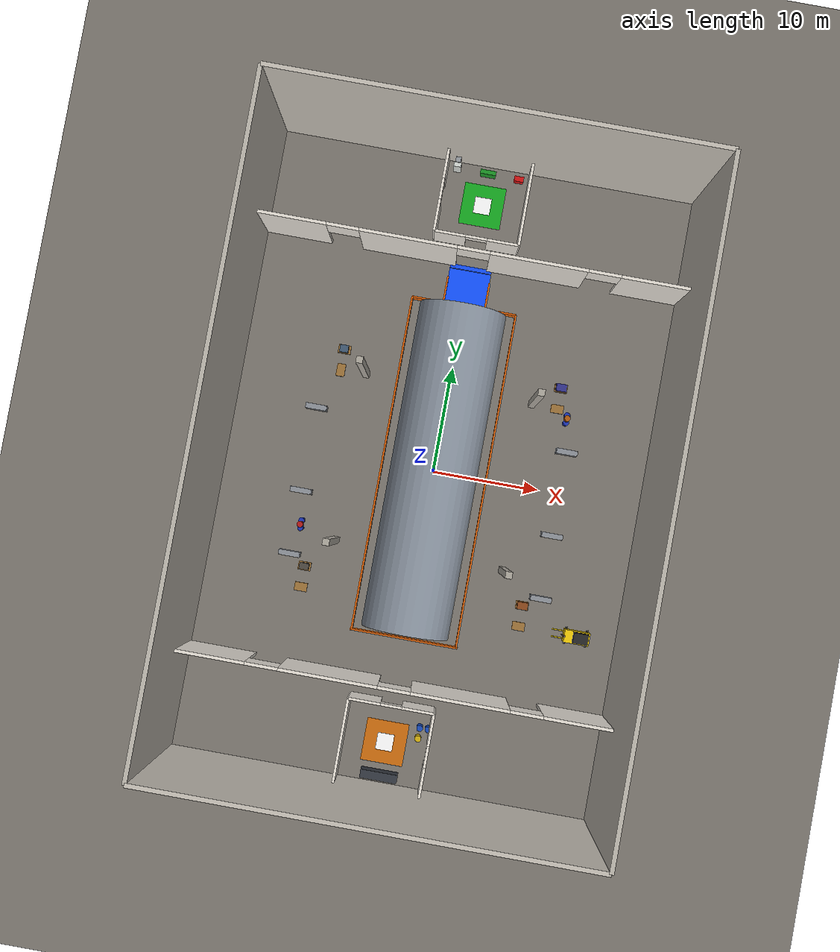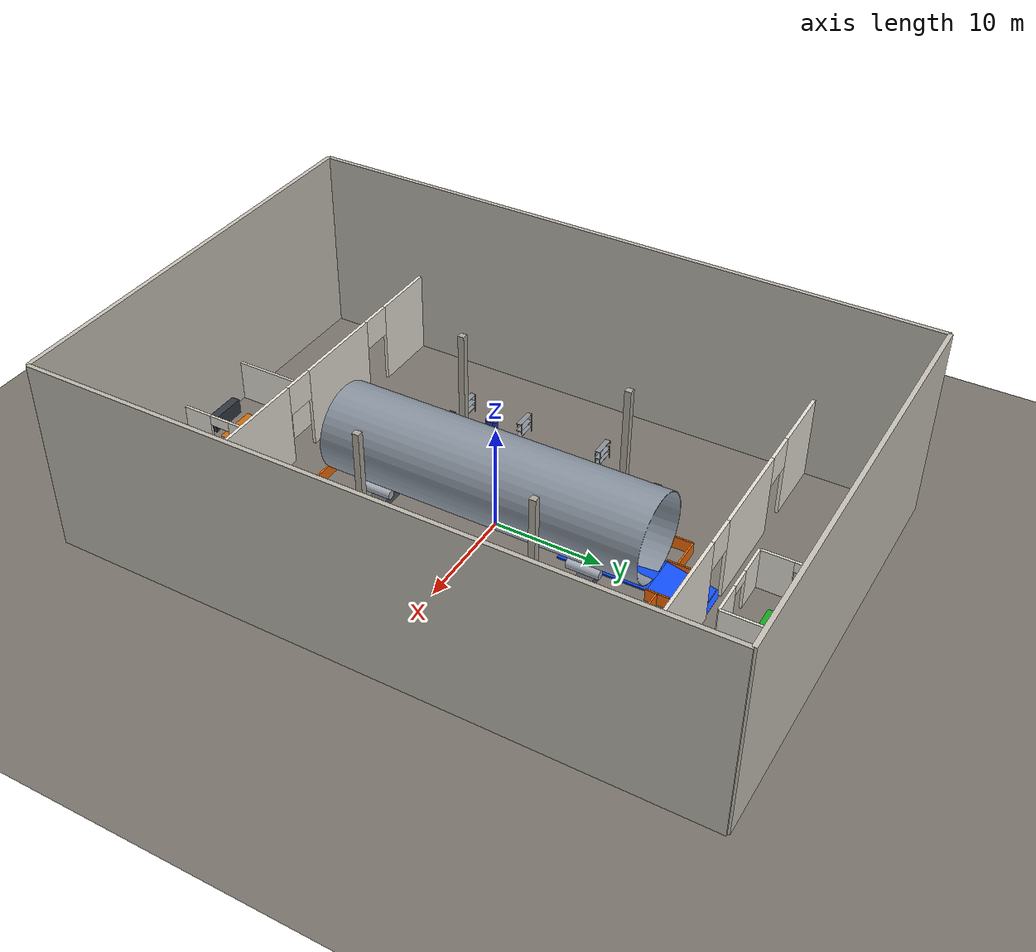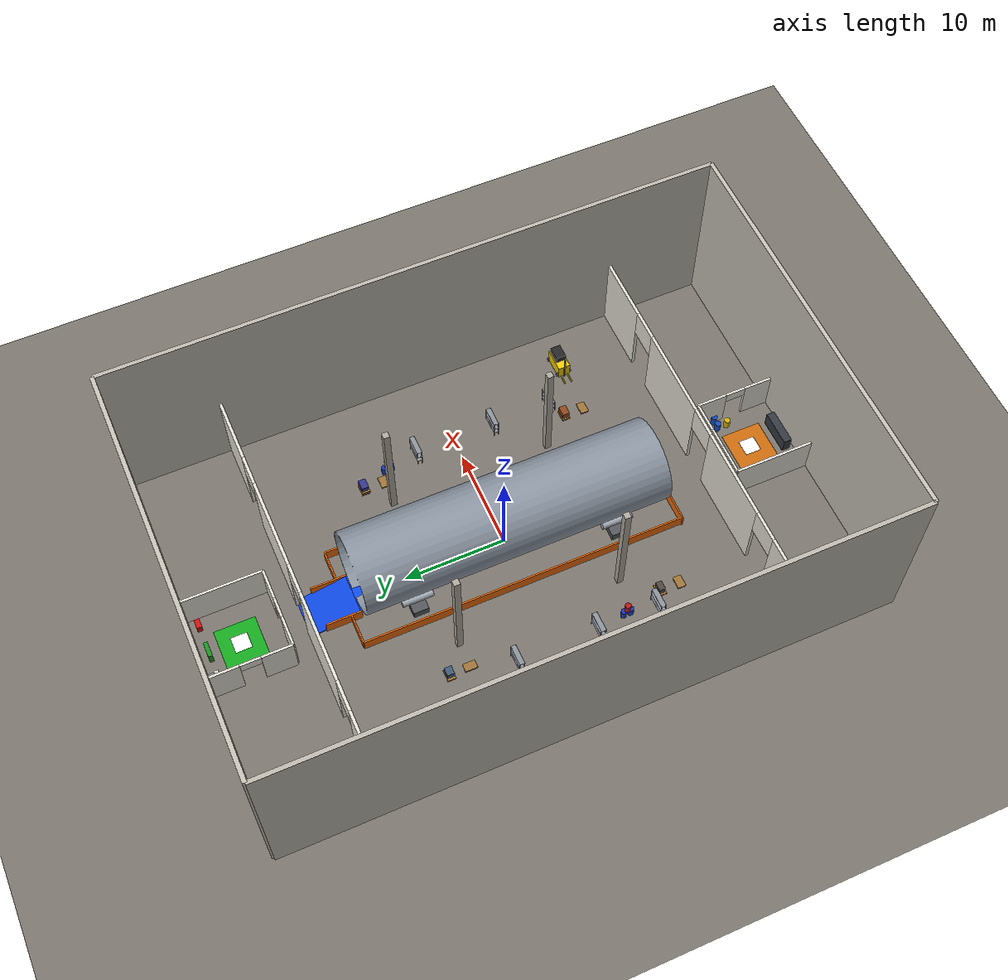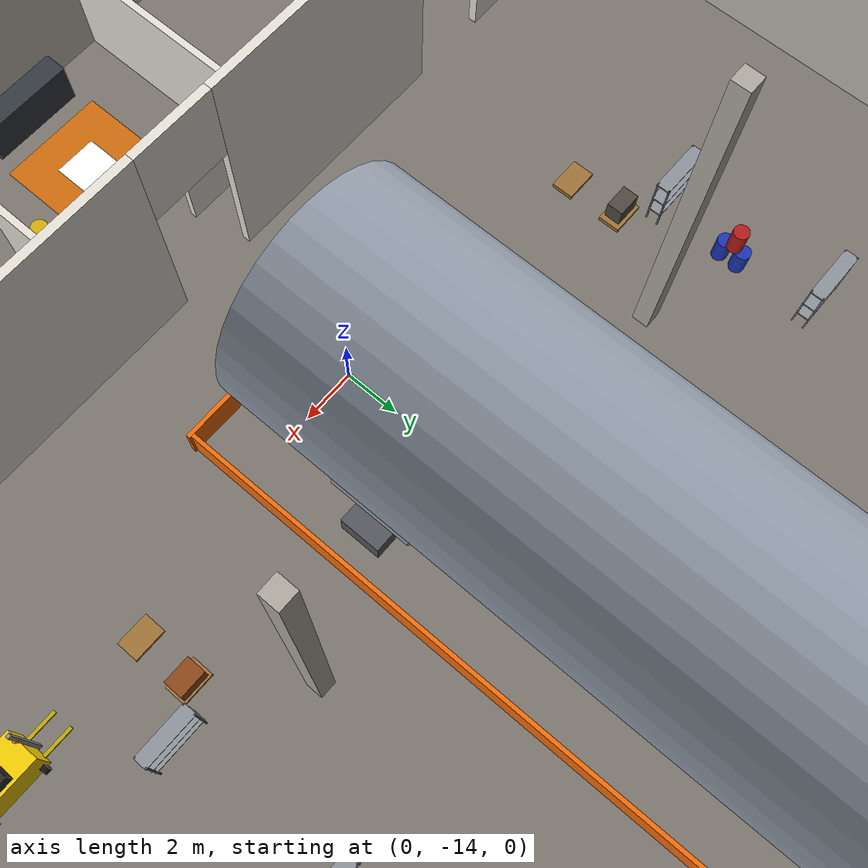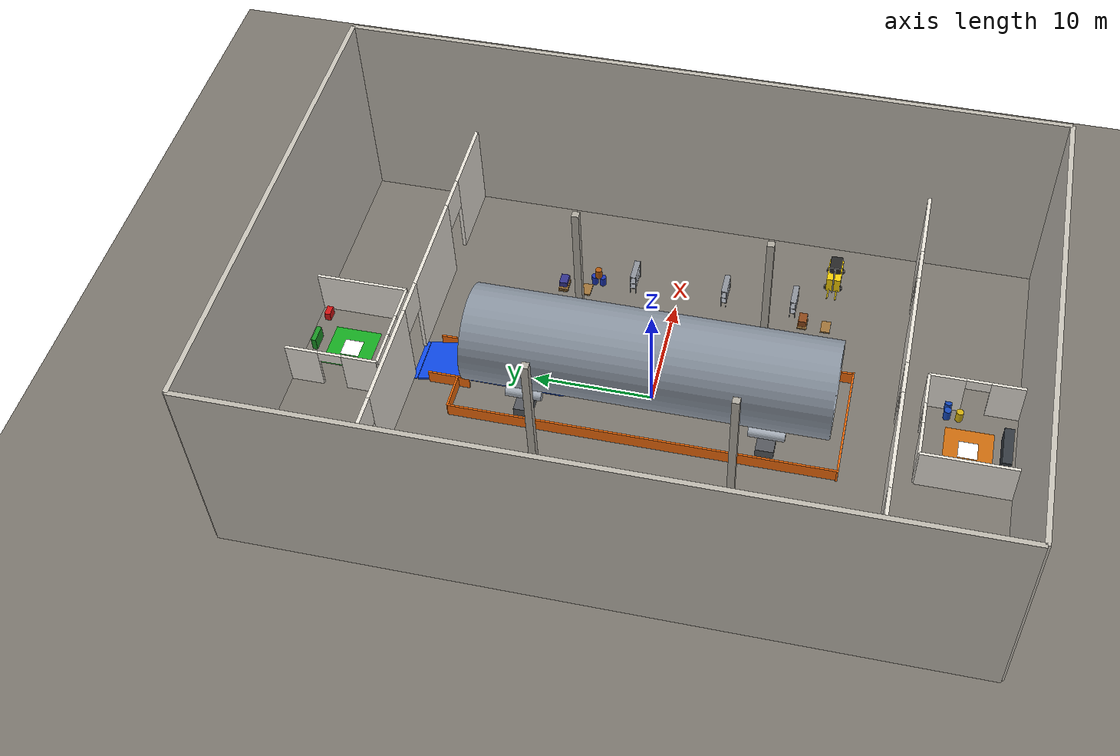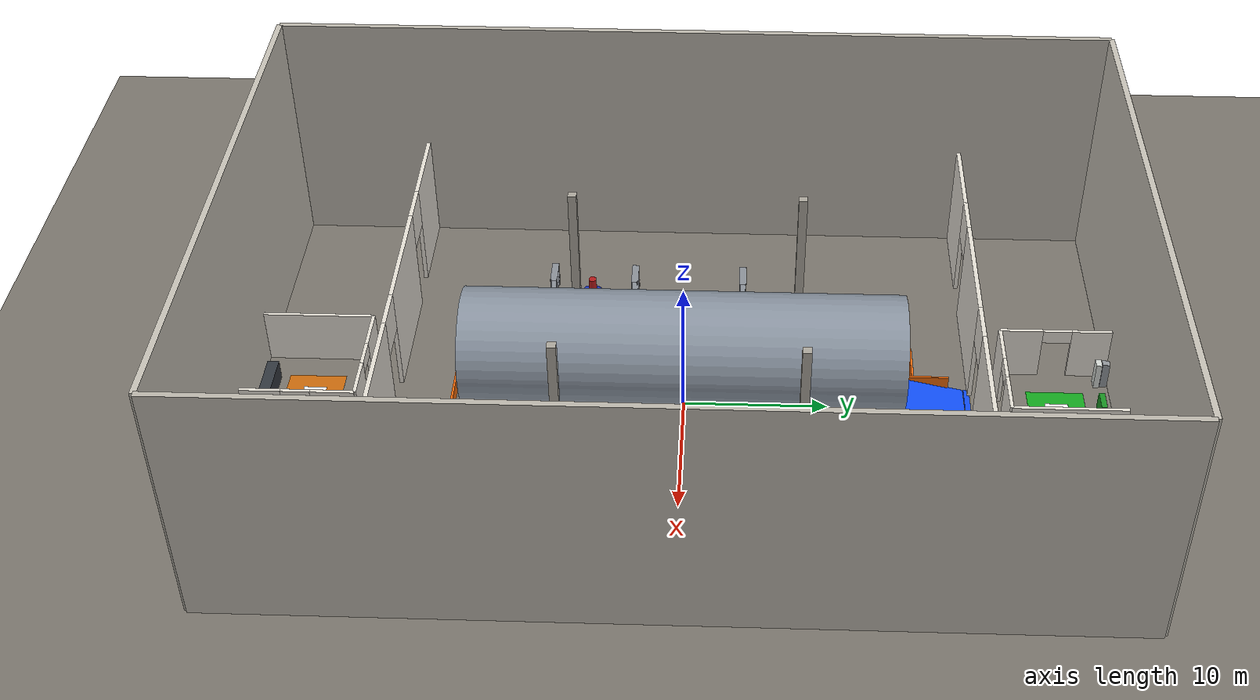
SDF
<sdf version="1.7">
 <world name="wind_tower_world">
  <gravity>0 0 -7.5</gravity>
  <physics type="ode">
   <max_step_size>0.004</max_step_size>
   <real_time_factor>1.0</real_time_factor>
   <real_time_update_rate>250</real_time_update_rate>
   <ode>
    <solver><type>quick</type><iters>50</iters><sor>1.3</sor></solver>
    <constraints>
     <cfm>0.0</cfm>
     <erp>0.2</erp>
     <contact_max_correcting_vel>0.2</contact_max_correcting_vel>
     <contact_surface_layer>0.001</contact_surface_layer>
    </constraints>
   </ode>
  </physics>
  <plugin name="gz::sim::systems::Physics" filename="libgz-sim-physics-system.so"/>
  <plugin name="gz::sim::systems::UserCommands" filename="libgz-sim-user-commands-system.so"/>
  <plugin name="gz::sim::systems::SceneBroadcaster" filename="libgz-sim-scene-broadcaster-system.so"/>
  <plugin name="gz::sim::systems::Contact" filename="libgz-sim-contact-system.so"/>
  <plugin name="gz::sim::systems::Sensors" filename="libgz-sim-sensors-system.so">
   <render_engine>ogre2</render_engine>
  </plugin>
  <plugin name="gz::sim::systems::Imu" filename="libgz-sim-imu-system.so"/>
  <plugin name="gz::sim::systems::NavSat" filename="libgz-sim-navsat-system.so"/>
  <scene>
   <ambient>0.50 0.50 0.52 1</ambient>
   <background>0.18 0.18 0.22 1</background>
   <shadows>true</shadows>
  </scene>
  <light type="directional" name="sun">
   <pose>0 0 25 0 0 0</pose>
   <diffuse>0.85 0.83 0.78 1</diffuse>
   <specular>0.25 0.24 0.22 1</specular>
   <direction>-0.3 0.2 -0.9</direction>
  </light>
  <light type="point" name="light_charge_A">
   <pose>0 25 6 0 0 0</pose>
   <diffuse>0.95 0.95 1.0 1</diffuse>
   <specular>0.1 0.1 0.1 1</specular>
   <attenuation>
    <range>15</range>
    <constant>0.4</constant>
    <linear>0.06</linear>
    <quadratic>0.008</quadratic>
   </attenuation>
   <cast_shadows>false</cast_shadows>
  </light>
  <light type="point" name="light_control_A">
   <pose>0 -25 6 0 0 0</pose>
   <diffuse>0.95 0.95 1.0 1</diffuse>
   <specular>0.1 0.1 0.1 1</specular>
   <attenuation>
    <range>15</range>
    <constant>0.4</constant>
    <linear>0.06</linear>
    <quadratic>0.008</quadratic>
   </attenuation>
   <cast_shadows>false</cast_shadows>
  </light>
  <model name="ground_plane">
   <static>true</static>
   <link name="link">
    <collision name="collision">
     <geometry><plane><normal>0 0 1</normal><size>200 200</size></plane></geometry>
     <surface>
      <friction><ode><mu>0.8</mu><mu2>0.8</mu2></ode></friction>
      <contact><ode><kp>500000</kp><kd>100</kd><max_vel>0.5</max_vel><min_depth>0.002</min_depth></ode></contact>
     </surface>
    </collision>
    <visual name="visual">
     <geometry><plane><normal>0 0 1</normal><size>200 200</size></plane></geometry>
     <material>
      <ambient>0.38 0.37 0.35 1</ambient>
      <diffuse>0.48 0.46 0.43 1</diffuse>
      <specular>0.05 0.05 0.05 1</specular>
     </material>
    </visual>
   </link>
  </model>
  <model name="wall_north">
   <static>true</static>
   <pose>0 30 9 0 0 0</pose>
   <link name="link">
    <collision name="col"><geometry><box><size>40 0.4 18</size></box></geometry></collision>
    <visual name="vis">
     <geometry><box><size>40 0.4 18</size></box></geometry>
     <material>
      <ambient>0.72 0.70 0.66 1</ambient>
      <diffuse>0.78 0.76 0.72 1</diffuse>
      <specular>0.03 0.03 0.03 1</specular>
     </material>
    </visual>
   </link>
  </model>
  <model name="wall_south">
   <static>true</static>
   <pose>0 -30 9 0 0 0</pose>
   <link name="link">
    <collision name="col"><geometry><box><size>40 0.4 18</size></box></geometry></collision>
    <visual name="vis">
     <geometry><box><size>40 0.4 18</size></box></geometry>
     <material>
      <ambient>0.72 0.70 0.66 1</ambient>
      <diffuse>0.78 0.76 0.72 1</diffuse>
      <specular>0.03 0.03 0.03 1</specular>
     </material>
    </visual>
   </link>
  </model>
  <model name="wall_east">
   <static>true</static>
   <pose>20 0 9 0 0 0</pose>
   <link name="link">
    <collision name="col"><geometry><box><size>0.4 60 18</size></box></geometry></collision>
    <visual name="vis">
     <geometry><box><size>0.4 60 18</size></box></geometry>
     <material>
      <ambient>0.68 0.66 0.62 1</ambient>
      <diffuse>0.74 0.72 0.68 1</diffuse>
      <specular>0.03 0.03 0.03 1</specular>
     </material>
    </visual>
   </link>
  </model>
  <model name="wall_west">
   <static>true</static>
   <pose>-20 0 9 0 0 0</pose>
   <link name="link">
    <collision name="col"><geometry><box><size>0.4 60 18</size></box></geometry></collision>
    <visual name="vis">
     <geometry><box><size>0.4 60 18</size></box></geometry>
     <material>
      <ambient>0.68 0.66 0.62 1</ambient>
      <diffuse>0.74 0.72 0.68 1</diffuse>
      <specular>0.03 0.03 0.03 1</specular>
     </material>
    </visual>
   </link>
  </model>
  <model name="sep_north_LW">
   <static>true</static>
   <pose>-16.75 20 4 0 0 0</pose>
   <link name="link">
    <collision name="col"><geometry><box><size>6.5 0.3 8</size></box></geometry></collision>
    <visual name="vis">
     <geometry><box><size>6.5 0.3 8</size></box></geometry>
     <material>
      <ambient>0.86 0.84 0.80 1</ambient>
      <diffuse>0.90 0.88 0.84 1</diffuse>
      <specular>0.04 0.04 0.04 1</specular>
     </material>
    </visual>
   </link>
  </model>
  <model name="sep_north_LM">
   <static>true</static>
   <pose>-6.0 20 4 0 0 0</pose>
   <link name="link">
    <collision name="col"><geometry><box><size>9.0 0.3 8</size></box></geometry></collision>
    <visual name="vis">
     <geometry><box><size>9.0 0.3 8</size></box></geometry>
     <material>
      <ambient>0.86 0.84 0.80 1</ambient>
      <diffuse>0.90 0.88 0.84 1</diffuse>
      <specular>0.04 0.04 0.04 1</specular>
     </material>
    </visual>
   </link>
  </model>
  <model name="sep_north_lintel">
   <static>true</static>
   <pose>0 20 6.5 0 0 0</pose>
   <link name="link">
    <collision name="col"><geometry><box><size>3.0 0.3 3.0</size></box></geometry></collision>
    <visual name="vis">
     <geometry><box><size>3.0 0.3 3.0</size></box></geometry>
     <material><ambient>0.86 0.84 0.80 1</ambient><diffuse>0.90 0.88 0.84 1</diffuse></material>
    </visual>
   </link>
  </model>
  <model name="sep_north_lintel_L">
   <static>true</static>
   <pose>-12 20 6.5 0 0 0</pose>
   <link name="link">
    <collision name="col"><geometry><box><size>3.0 0.3 3.0</size></box></geometry></collision>
    <visual name="vis">
     <geometry><box><size>3.0 0.3 3.0</size></box></geometry>
     <material><ambient>0.86 0.84 0.80 1</ambient><diffuse>0.90 0.88 0.84 1</diffuse></material>
    </visual>
   </link>
  </model>
  <model name="sep_north_RM">
   <static>true</static>
   <pose>6.0 20 4 0 0 0</pose>
   <link name="link">
    <collision name="col"><geometry><box><size>9.0 0.3 8</size></box></geometry></collision>
    <visual name="vis">
     <geometry><box><size>9.0 0.3 8</size></box></geometry>
     <material>
      <ambient>0.86 0.84 0.80 1</ambient>
      <diffuse>0.90 0.88 0.84 1</diffuse>
      <specular>0.04 0.04 0.04 1</specular>
     </material>
    </visual>
   </link>
  </model>
  <model name="sep_north_RE">
   <static>true</static>
   <pose>16.75 20 4 0 0 0</pose>
   <link name="link">
    <collision name="col"><geometry><box><size>6.5 0.3 8</size></box></geometry></collision>
    <visual name="vis">
     <geometry><box><size>6.5 0.3 8</size></box></geometry>
     <material>
      <ambient>0.86 0.84 0.80 1</ambient>
      <diffuse>0.90 0.88 0.84 1</diffuse>
      <specular>0.04 0.04 0.04 1</specular>
     </material>
    </visual>
   </link>
  </model>
  <model name="sep_north_lintel_R">
   <static>true</static>
   <pose>12 20 6.5 0 0 0</pose>
   <link name="link">
    <collision name="col"><geometry><box><size>3.0 0.3 3.0</size></box></geometry></collision>
    <visual name="vis">
     <geometry><box><size>3.0 0.3 3.0</size></box></geometry>
     <material><ambient>0.86 0.84 0.80 1</ambient><diffuse>0.90 0.88 0.84 1</diffuse></material>
    </visual>
   </link>
  </model>
  <model name="sep_south_LE">
   <static>true</static>
   <pose>-16.75 -20 4 0 0 0</pose>
   <link name="link">
    <collision name="col"><geometry><box><size>6.5 0.3 8</size></box></geometry></collision>
    <visual name="vis">
     <geometry><box><size>6.5 0.3 8</size></box></geometry>
     <material>
      <ambient>0.86 0.84 0.80 1</ambient>
      <diffuse>0.90 0.88 0.84 1</diffuse>
      <specular>0.04 0.04 0.04 1</specular>
     </material>
    </visual>
   </link>
  </model>
  <model name="sep_south_lintel_L">
   <static>true</static>
   <pose>-12 -20 6.5 0 0 0</pose>
   <link name="link">
    <collision name="col"><geometry><box><size>3.0 0.3 3.0</size></box></geometry></collision>
    <visual name="vis">
     <geometry><box><size>3.0 0.3 3.0</size></box></geometry>
     <material><ambient>0.86 0.84 0.80 1</ambient><diffuse>0.90 0.88 0.84 1</diffuse></material>
    </visual>
   </link>
  </model>
  <model name="sep_south_LM">
   <static>true</static>
   <pose>-6.0 -20 4 0 0 0</pose>
   <link name="link">
    <collision name="col"><geometry><box><size>9.0 0.3 8</size></box></geometry></collision>
    <visual name="vis">
     <geometry><box><size>9.0 0.3 8</size></box></geometry>
     <material>
      <ambient>0.86 0.84 0.80 1</ambient>
      <diffuse>0.90 0.88 0.84 1</diffuse>
      <specular>0.04 0.04 0.04 1</specular>
     </material>
    </visual>
   </link>
  </model>
  <model name="sep_south_lintel">
   <static>true</static>
   <pose>0 -20 6.5 0 0 0</pose>
   <link name="link">
    <collision name="col"><geometry><box><size>3.0 0.3 3.0</size></box></geometry></collision>
    <visual name="vis">
     <geometry><box><size>3.0 0.3 3.0</size></box></geometry>
     <material><ambient>0.86 0.84 0.80 1</ambient><diffuse>0.90 0.88 0.84 1</diffuse></material>
    </visual>
   </link>
  </model>
  <model name="sep_south_RM">
   <static>true</static>
   <pose>6.0 -20 4 0 0 0</pose>
   <link name="link">
    <collision name="col"><geometry><box><size>9.0 0.3 8</size></box></geometry></collision>
    <visual name="vis">
     <geometry><box><size>9.0 0.3 8</size></box></geometry>
     <material>
      <ambient>0.86 0.84 0.80 1</ambient>
      <diffuse>0.90 0.88 0.84 1</diffuse>
      <specular>0.04 0.04 0.04 1</specular>
     </material>
    </visual>
   </link>
  </model>
  <model name="sep_south_lintel_R">
   <static>true</static>
   <pose>12 -20 6.5 0 0 0</pose>
   <link name="link">
    <collision name="col"><geometry><box><size>3.0 0.3 3.0</size></box></geometry></collision>
    <visual name="vis">
     <geometry><box><size>3.0 0.3 3.0</size></box></geometry>
     <material><ambient>0.86 0.84 0.80 1</ambient><diffuse>0.90 0.88 0.84 1</diffuse></material>
    </visual>
   </link>
  </model>
  <model name="sep_south_RE">
   <static>true</static>
   <pose>16.75 -20 4 0 0 0</pose>
   <link name="link">
    <collision name="col"><geometry><box><size>6.5 0.3 8</size></box></geometry></collision>
    <visual name="vis">
     <geometry><box><size>6.5 0.3 8</size></box></geometry>
     <material>
      <ambient>0.86 0.84 0.80 1</ambient>
      <diffuse>0.90 0.88 0.84 1</diffuse>
      <specular>0.04 0.04 0.04 1</specular>
     </material>
    </visual>
   </link>
  </model>
  <model name="charge_front_L">
   <static>true</static>
   <pose>-2.5 22 2 0 0 0</pose>
   <link name="link">
    <collision name="col"><geometry><box><size>3.0 0.25 4</size></box></geometry></collision>
    <visual name="vis">
     <geometry><box><size>3.0 0.25 4</size></box></geometry>
     <material><ambient>0.86 0.84 0.80 1</ambient><diffuse>0.90 0.88 0.84 1</diffuse></material>
    </visual>
   </link>
  </model>
  <model name="charge_front_R">
   <static>true</static>
   <pose>2.5 22 2 0 0 0</pose>
   <link name="link">
    <collision name="col"><geometry><box><size>3.0 0.25 4</size></box></geometry></collision>
    <visual name="vis">
     <geometry><box><size>3.0 0.25 4</size></box></geometry>
     <material><ambient>0.86 0.84 0.80 1</ambient><diffuse>0.90 0.88 0.84 1</diffuse></material>
    </visual>
   </link>
  </model>
  <model name="charge_front_lintel">
   <static>true</static>
   <pose>0 22 3.5 0 0 0</pose>
   <link name="link">
    <collision name="col"><geometry><box><size>2.0 0.25 1.0</size></box></geometry></collision>
    <visual name="vis">
     <geometry><box><size>2.0 0.25 1.0</size></box></geometry>
     <material><ambient>0.86 0.84 0.80 1</ambient><diffuse>0.90 0.88 0.84 1</diffuse></material>
    </visual>
   </link>
  </model>
  <model name="charge_wall_W_N">
   <static>true</static>
   <pose>-4 28.5 2 0 0 0</pose>
   <link name="link">
    <collision name="col"><geometry><box><size>0.25 3 4</size></box></geometry></collision>
    <visual name="vis">
     <geometry><box><size>0.25 3 4</size></box></geometry>
     <material><ambient>0.86 0.84 0.80 1</ambient><diffuse>0.90 0.88 0.84 1</diffuse></material>
    </visual>
   </link>
  </model>
  <model name="charge_wall_W_lintel">
   <static>true</static>
   <pose>-4 26 3.5 0 0 0</pose>
   <link name="link">
    <collision name="col"><geometry><box><size>0.25 2 1</size></box></geometry></collision>
    <visual name="vis">
     <geometry><box><size>0.25 2 1</size></box></geometry>
     <material><ambient>0.86 0.84 0.80 1</ambient><diffuse>0.90 0.88 0.84 1</diffuse></material>
    </visual>
   </link>
  </model>
  <model name="charge_wall_W_S">
   <static>true</static>
   <pose>-4 23.5 2 0 0 0</pose>
   <link name="link">
    <collision name="col"><geometry><box><size>0.25 3 4</size></box></geometry></collision>
    <visual name="vis">
     <geometry><box><size>0.25 3 4</size></box></geometry>
     <material><ambient>0.86 0.84 0.80 1</ambient><diffuse>0.90 0.88 0.84 1</diffuse></material>
    </visual>
   </link>
  </model>
  <model name="charge_wall_E">
   <static>true</static>
   <pose>4 26 2 0 0 0</pose>
   <link name="link">
    <collision name="col"><geometry><box><size>0.25 8 4</size></box></geometry></collision>
    <visual name="vis">
     <geometry><box><size>0.25 8 4</size></box></geometry>
     <material><ambient>0.86 0.84 0.80 1</ambient><diffuse>0.90 0.88 0.84 1</diffuse></material>
    </visual>
   </link>
  </model>
  <model name="floor_marker_charge">
   <static>true</static>
   <pose>0 26 0.005 0 0 0</pose>
   <link name="link">
    <collision name="col"><geometry><box><size>4.0 4.0 0.01</size></box></geometry></collision>
    <visual name="vis">
     <geometry><box><size>4.0 4.0 0.01</size></box></geometry>
     <material>
      <ambient>0.05 0.60 0.10 0.85</ambient>
      <diffuse>0.06 0.75 0.12 0.85</diffuse>
      <specular>0.10 0.20 0.10 1</specular>
     </material>
    </visual>
    <visual name="battery_icon_floor">
     <pose>0 0 0.02 0 0 0</pose>
     <geometry><plane><normal>0 0 1</normal><size>1.6 1.6</size></plane></geometry>
     <material>
      <ambient>1 1 1 1</ambient>
      <diffuse>1 1 1 1</diffuse>
      <pbr>
       <metal>
        <albedo_map>file:///home/dmore/ROS2_Wind_Tower_Inspection/ros2_ws/src/wind_tower_inspection_behaviour/static/battery.png</albedo_map>
       </metal>
      </pbr>
     </material>
    </visual>
   </link>
  </model>
  <model name="charging_dock">
   <static>true</static>
   <pose>0 29 0.6 0 0 3.14159</pose>
   <link name="link">
    <collision name="col"><geometry><box><size>1.5 0.4 1.2</size></box></geometry></collision>
    <visual name="vis">
     <geometry><box><size>1.5 0.4 1.2</size></box></geometry>
     <material>
      <ambient>0.08 0.48 0.12 1</ambient>
      <diffuse>0.10 0.58 0.14 1</diffuse>
      <specular>0.20 0.20 0.20 1</specular>
     </material>
    </visual>
   </link>
  </model>
  <model name="electric_cabinet">
   <static>true</static>
   <pose>-3 29 1.0 0 0 0</pose>
   <link name="link">
    <collision name="col"><geometry><box><size>0.7 0.4 2.0</size></box></geometry></collision>
    <visual name="vis">
     <geometry><box><size>0.7 0.4 2.0</size></box></geometry>
     <material>
      <ambient>0.78 0.80 0.78 1</ambient>
      <diffuse>0.84 0.86 0.84 1</diffuse>
      <specular>0.15 0.15 0.15 1</specular>
     </material>
    </visual>
   </link>
  </model>
  <model name="toolbox">
   <static>true</static>
   <pose>3 29 0.4 0 0 0</pose>
   <link name="link">
    <collision name="col"><geometry><box><size>0.9 0.5 0.8</size></box></geometry></collision>
    <visual name="vis">
     <geometry><box><size>0.9 0.5 0.8</size></box></geometry>
     <material>
      <ambient>0.72 0.06 0.06 1</ambient>
      <diffuse>0.82 0.07 0.07 1</diffuse>
      <specular>0.30 0.30 0.30 1</specular>
     </material>
    </visual>
   </link>
  </model>
  <model name="ctrl_front_L">
   <static>true</static>
   <pose>-2.5 -22 2 0 0 0</pose>
   <link name="link">
    <collision name="col"><geometry><box><size>3.0 0.25 4</size></box></geometry></collision>
    <visual name="vis">
     <geometry><box><size>3.0 0.25 4</size></box></geometry>
     <material><ambient>0.86 0.84 0.80 1</ambient><diffuse>0.90 0.88 0.84 1</diffuse></material>
    </visual>
   </link>
  </model>
  <model name="ctrl_front_R">
   <static>true</static>
   <pose>2.5 -22 2 0 0 0</pose>
   <link name="link">
    <collision name="col"><geometry><box><size>3.0 0.25 4</size></box></geometry></collision>
    <visual name="vis">
     <geometry><box><size>3.0 0.25 4</size></box></geometry>
     <material><ambient>0.86 0.84 0.80 1</ambient><diffuse>0.90 0.88 0.84 1</diffuse></material>
    </visual>
   </link>
  </model>
  <model name="ctrl_front_lintel">
   <static>true</static>
   <pose>0 -22 3.5 0 0 0</pose>
   <link name="link">
    <collision name="col"><geometry><box><size>2.0 0.25 1.0</size></box></geometry></collision>
    <visual name="vis">
     <geometry><box><size>2.0 0.25 1.0</size></box></geometry>
     <material><ambient>0.86 0.84 0.80 1</ambient><diffuse>0.90 0.88 0.84 1</diffuse></material>
    </visual>
   </link>
  </model>
  <model name="ctrl_wall_W">
   <static>true</static>
   <pose>-4 -26 2 0 0 0</pose>
   <link name="link">
    <collision name="col"><geometry><box><size>0.25 8 4</size></box></geometry></collision>
    <visual name="vis">
     <geometry><box><size>0.25 8 4</size></box></geometry>
     <material><ambient>0.86 0.84 0.80 1</ambient><diffuse>0.90 0.88 0.84 1</diffuse></material>
    </visual>
   </link>
  </model>
  <model name="ctrl_wall_E_N">
   <static>true</static>
   <pose>4 -23.5 2 0 0 0</pose>
   <link name="link">
    <collision name="col"><geometry><box><size>0.25 3 4</size></box></geometry></collision>
    <visual name="vis">
     <geometry><box><size>0.25 3 4</size></box></geometry>
     <material><ambient>0.86 0.84 0.80 1</ambient><diffuse>0.90 0.88 0.84 1</diffuse></material>
    </visual>
   </link>
  </model>
  <model name="ctrl_wall_E_lintel">
   <static>true</static>
   <pose>4 -26 3.5 0 0 0</pose>
   <link name="link">
    <collision name="col"><geometry><box><size>0.25 2 1</size></box></geometry></collision>
    <visual name="vis">
     <geometry><box><size>0.25 2 1</size></box></geometry>
     <material><ambient>0.86 0.84 0.80 1</ambient><diffuse>0.90 0.88 0.84 1</diffuse></material>
    </visual>
   </link>
  </model>
  <model name="ctrl_wall_E_S">
   <static>true</static>
   <pose>4 -28.5 2 0 0 0</pose>
   <link name="link">
    <collision name="col"><geometry><box><size>0.25 3 4</size></box></geometry></collision>
    <visual name="vis">
     <geometry><box><size>0.25 3 4</size></box></geometry>
     <material><ambient>0.86 0.84 0.80 1</ambient><diffuse>0.90 0.88 0.84 1</diffuse></material>
    </visual>
   </link>
  </model>
  <model name="floor_marker_maint">
   <static>true</static>
   <pose>0 -26 0.005 0 0 0</pose>
   <link name="link">
    <collision name="col"><geometry><box><size>4.0 4.0 0.01</size></box></geometry></collision>
    <visual name="vis">
     <geometry><box><size>4.0 4.0 0.01</size></box></geometry>
     <material>
      <ambient>0.75 0.38 0.02 0.85</ambient>
      <diffuse>0.90 0.46 0.03 0.85</diffuse>
      <specular>0.20 0.12 0.02 1</specular>
     </material>
    </visual>
    <visual name="tool_icon_floor">
     <pose>0 0 0.02 0 0 0</pose>
     <geometry><plane><normal>0 0 1</normal><size>1.6 1.6</size></plane></geometry>
     <material>
      <ambient>1 1 1 1</ambient>
      <diffuse>1 1 1 1</diffuse>
      <pbr>
       <metal>
        <albedo_map>file:///home/dmore/ROS2_Wind_Tower_Inspection/ros2_ws/src/wind_tower_inspection_behaviour/static/tool.png</albedo_map>
       </metal>
      </pbr>
     </material>
    </visual>
   </link>
  </model>
  <model name="control_console">
   <static>true</static>
   <pose>0 -29 0.75 0 0 0</pose>
   <link name="link">
    <collision name="col"><geometry><box><size>3.5 0.8 1.5</size></box></geometry></collision>
    <visual name="vis">
     <geometry><box><size>3.5 0.8 1.5</size></box></geometry>
     <material>
      <ambient>0.16 0.18 0.20 1</ambient>
      <diffuse>0.20 0.22 0.25 1</diffuse>
      <specular>0.25 0.25 0.25 1</specular>
     </material>
    </visual>
   </link>
  </model>
  <model name="shelf_storage">
   <static>true</static>
   <pose>-3 29.5 1.0 0 0 0</pose>
   <link name="link">
    <collision name="col"><geometry><box><size>0.5 0.5 2.0</size></box></geometry></collision>
    <visual name="vis">
     <geometry><box><size>0.5 0.5 2.0</size></box></geometry>
     <material>
      <ambient>0.50 0.52 0.54 1</ambient>
      <diffuse>0.58 0.60 0.62 1</diffuse>
      <specular>0.20 0.20 0.20 1</specular>
     </material>
    </visual>
   </link>
  </model>
  <model name="barrel_blue_1">
   <static>true</static>
   <pose>3 -24 0.5 0 0 0</pose>
   <link name="link">
    <collision name="col">
     <geometry><cylinder><radius>0.3</radius><length>1.0</length></cylinder></geometry>
    </collision>
    <visual name="vis">
     <geometry><cylinder><radius>0.3</radius><length>1.0</length></cylinder></geometry>
     <material>
      <ambient>0.06 0.22 0.60 1</ambient>
      <diffuse>0.08 0.28 0.72 1</diffuse>
      <specular>0.20 0.20 0.20 1</specular>
     </material>
    </visual>
   </link>
  </model>
  <model name="barrel_blue_2">
   <static>true</static>
   <pose>3.8 -24 0.5 0 0 0</pose>
   <link name="link">
    <collision name="col">
     <geometry><cylinder><radius>0.3</radius><length>1.0</length></cylinder></geometry>
    </collision>
    <visual name="vis">
     <geometry><cylinder><radius>0.3</radius><length>1.0</length></cylinder></geometry>
     <material>
      <ambient>0.06 0.22 0.60 1</ambient>
      <diffuse>0.08 0.28 0.72 1</diffuse>
      <specular>0.20 0.20 0.20 1</specular>
     </material>
    </visual>
   </link>
  </model>
  <model name="barrel_yellow">
   <static>true</static>
   <pose>3 -25 0.5 0 0 0</pose>
   <link name="link">
    <collision name="col">
     <geometry><cylinder><radius>0.3</radius><length>1.0</length></cylinder></geometry>
    </collision>
    <visual name="vis">
     <geometry><cylinder><radius>0.3</radius><length>1.0</length></cylinder></geometry>
     <material>
      <ambient>0.72 0.58 0.04 1</ambient>
      <diffuse>0.82 0.68 0.05 1</diffuse>
      <specular>0.20 0.20 0.20 1</specular>
     </material>
    </visual>
   </link>
  </model>
  <model name="column_NE">
   <static>true</static>
   <pose>8 8 6 0 0 0</pose>
   <link name="link">
    <collision name="col"><geometry><box><size>0.6 0.6 12</size></box></geometry></collision>
    <visual name="vis">
     <geometry><box><size>0.6 0.6 12</size></box></geometry>
     <material>
      <ambient>0.62 0.60 0.57 1</ambient>
      <diffuse>0.68 0.66 0.62 1</diffuse>
      <specular>0.04 0.04 0.04 1</specular>
     </material>
    </visual>
   </link>
  </model>
  <model name="column_NW">
   <static>true</static>
   <pose>-8 8 6 0 0 0</pose>
   <link name="link">
    <collision name="col"><geometry><box><size>0.6 0.6 12</size></box></geometry></collision>
    <visual name="vis">
     <geometry><box><size>0.6 0.6 12</size></box></geometry>
     <material>
      <ambient>0.62 0.60 0.57 1</ambient>
      <diffuse>0.68 0.66 0.62 1</diffuse>
      <specular>0.04 0.04 0.04 1</specular>
     </material>
    </visual>
   </link>
  </model>
  <model name="column_SE">
   <static>true</static>
   <pose>8 -8 6 0 0 0</pose>
   <link name="link">
    <collision name="col"><geometry><box><size>0.6 0.6 12</size></box></geometry></collision>
    <visual name="vis">
     <geometry><box><size>0.6 0.6 12</size></box></geometry>
     <material>
      <ambient>0.62 0.60 0.57 1</ambient>
      <diffuse>0.68 0.66 0.62 1</diffuse>
      <specular>0.04 0.04 0.04 1</specular>
     </material>
    </visual>
   </link>
  </model>
  <model name="column_SW">
   <static>true</static>
   <pose>-8 -8 6 0 0 0</pose>
   <link name="link">
    <collision name="col"><geometry><box><size>0.6 0.6 12</size></box></geometry></collision>
    <visual name="vis">
     <geometry><box><size>0.6 0.6 12</size></box></geometry>
     <material>
      <ambient>0.62 0.60 0.57 1</ambient>
      <diffuse>0.68 0.66 0.62 1</diffuse>
      <specular>0.04 0.04 0.04 1</specular>
     </material>
    </visual>
   </link>
  </model>
  <model name="wind_tower_tube">
   <static>false</static>
   <pose>-4 15 1 1.5708 0 0</pose>
   <link name="tube_link">
    <inertial>
     <mass>2000</mass>
     <inertia><ixx>155000</ixx><ixy>0</ixy><ixz>0</ixz><iyy>155000</iyy><iyz>0</iyz><izz>32000</izz></inertia>
    </inertial>
    <visual name="visual">
     <geometry><mesh><uri>model://TRAMO_TORRE.STL</uri><scale>0.001 0.001 0.001</scale></mesh></geometry>
     <material>
      <ambient>0.48 0.52 0.56 1</ambient>
      <diffuse>0.55 0.59 0.64 1</diffuse>
      <specular>0.35 0.35 0.35 1</specular>
     </material>
    </visual>
    <collision name="collision">
     <geometry><mesh><uri>model://TRAMO_TORRE.STL</uri><scale>0.001 0.001 0.001</scale></mesh></geometry>
    </collision>
   </link>
   <joint name="turner_joint" type="revolute">
    <parent>world</parent>
    <child>tube_link</child>
    <pose>4.0 4.0 0 0 0 0</pose>
    <axis>
     <xyz expressed_in="__model__">0 0 1</xyz>
     <limit><lower>-1e16</lower><upper>1e16</upper></limit>
     <dynamics><damping>2.0</damping><friction>0.1</friction></dynamics>
    </axis>
   </joint>
   <plugin filename="gz-sim-joint-controller-system" name="gz::sim::systems::JointController">
    <joint_name>turner_joint</joint_name>
    <use_force_commands>false</use_force_commands>
    <initial_velocity>0.0</initial_velocity>
   </plugin>
   <plugin filename="gz-sim-joint-state-publisher-system" name="gz::sim::systems::JointStatePublisher"/>
  </model>
  <model name="roller_frame_north">
   <static>true</static>
   <pose>0 10 0.4 0 0 0</pose>
   <link name="link">
    <collision name="col"><geometry><box><size>8.0 1.5 0.8</size></box></geometry></collision>
    <visual name="vis">
     <geometry><box><size>8.0 1.5 0.8</size></box></geometry>
     <material>
      <ambient>0.28 0.29 0.30 1</ambient>
      <diffuse>0.33 0.34 0.36 1</diffuse>
      <specular>0.12 0.12 0.12 1</specular>
     </material>
    </visual>
   </link>
  </model>
  <model name="roller_N_right">
   <static>true</static>
   <pose>3.11 10 1.89 1.5708 0 0</pose>
   <link name="link">
    <collision name="col">
     <geometry><cylinder><radius>0.4</radius><length>3.0</length></cylinder></geometry>
    </collision>
    <visual name="vis">
     <geometry><cylinder><radius>0.4</radius><length>3.0</length></cylinder></geometry>
     <material>
      <ambient>0.55 0.57 0.60 1</ambient>
      <diffuse>0.65 0.68 0.72 1</diffuse>
      <specular>0.70 0.70 0.70 1</specular>
     </material>
    </visual>
   </link>
  </model>
  <model name="roller_N_left">
   <static>true</static>
   <pose>-3.11 10 1.89 1.5708 0 0</pose>
   <link name="link">
    <collision name="col">
     <geometry><cylinder><radius>0.4</radius><length>3.0</length></cylinder></geometry>
    </collision>
    <visual name="vis">
     <geometry><cylinder><radius>0.4</radius><length>3.0</length></cylinder></geometry>
     <material>
      <ambient>0.55 0.57 0.60 1</ambient>
      <diffuse>0.65 0.68 0.72 1</diffuse>
      <specular>0.70 0.70 0.70 1</specular>
     </material>
    </visual>
   </link>
  </model>
  <model name="ramp_north_entry">
   <static>true</static>
   <pose>0 19.8 -0.056 -0.115 0 0</pose>
   <link name="link">
    <collision name="col">
     <geometry><box><size>4.0 0.4 0.15</size></box></geometry>
     <surface>
      <friction><ode><mu>3.0</mu><mu2>3.0</mu2><slip1>0.0</slip1><slip2>0.0</slip2></ode></friction>
      <contact><ode><kp>1000000</kp><kd>50</kd><max_vel>0.1</max_vel><min_depth>0.001</min_depth></ode></contact>
     </surface>
    </collision>
    <visual name="vis">
     <geometry><box><size>4.0 0.4 0.15</size></box></geometry>
     <material>
      <ambient>0.04 0.20 0.55 1</ambient>
      <diffuse>0.06 0.30 0.95 1</diffuse>
      <specular>0.25 0.25 0.25 1</specular>
     </material>
    </visual>
   </link>
  </model>
  <model name="ramp_north">
   <static>true</static>
   <pose>0 17.3 0.497 -0.230 0 0</pose>
   <link name="link">
    <collision name="col">
     <geometry><box><size>4.0 4.6 0.15</size></box></geometry>
     <surface>
      <friction><ode><mu>3.0</mu><mu2>3.0</mu2><slip1>0.0</slip1><slip2>0.0</slip2></ode></friction>
      <contact><ode><kp>1000000</kp><kd>50</kd><max_vel>0.1</max_vel><min_depth>0.001</min_depth></ode></contact>
     </surface>
    </collision>
    <visual name="vis">
     <geometry><box><size>4.0 4.6 0.15</size></box></geometry>
     <material>
      <ambient>0.04 0.20 0.55 1</ambient>
      <diffuse>0.06 0.30 0.95 1</diffuse>
      <specular>0.25 0.25 0.25 1</specular>
     </material>
    </visual>
   </link>
  </model>
  <model name="ramp_inner">
   <static>true</static>
   <pose>0 11.05 0.972 0.01161 0 0</pose>
   <link name="link">
    <collision name="col">
     <geometry><box><size>4.0 8.1 0.15</size></box></geometry>
     <surface>
      <friction><ode><mu>3.0</mu><mu2>3.0</mu2><slip1>0.0</slip1><slip2>0.0</slip2></ode></friction>
      <contact><ode><kp>1000000</kp><kd>50</kd><max_vel>0.1</max_vel><min_depth>0.001</min_depth></ode></contact>
     </surface>
    </collision>
    <visual name="vis">
     <geometry><box><size>4.0 8.1 0.15</size></box></geometry>
     <material>
      <ambient>0.04 0.20 0.55 1</ambient>
      <diffuse>0.06 0.30 0.95 1</diffuse>
      <specular>0.25 0.25 0.25 1</specular>
     </material>
    </visual>
   </link>
  </model>
  <model name="barrier_south">
   <static>true</static>
   <pose>0 -16 0.6 0 0 0</pose>
   <link name="link">
    <collision name="col"><geometry><box><size>10.3 0.15 1.2</size></box></geometry></collision>
    <visual name="vis">
     <geometry><box><size>10.3 0.15 1.2</size></box></geometry>
     <material>
      <ambient>0.85 0.35 0.03 1</ambient>
      <diffuse>0.95 0.42 0.04 1</diffuse>
      <specular>0.25 0.25 0.25 1</specular>
     </material>
    </visual>
   </link>
  </model>
  <model name="barrier_east">
   <static>true</static>
   <pose>5 0 0.6 0 0 0</pose>
   <link name="link">
    <collision name="col"><geometry><box><size>0.15 32.0 1.2</size></box></geometry></collision>
    <visual name="vis">
     <geometry><box><size>0.15 32.0 1.2</size></box></geometry>
     <material>
      <ambient>0.85 0.35 0.03 1</ambient>
      <diffuse>0.95 0.42 0.04 1</diffuse>
      <specular>0.25 0.25 0.25 1</specular>
     </material>
    </visual>
   </link>
  </model>
  <model name="barrier_west">
   <static>true</static>
   <pose>-5 0 0.6 0 0 0</pose>
   <link name="link">
    <collision name="col"><geometry><box><size>0.15 32.0 1.2</size></box></geometry></collision>
    <visual name="vis">
     <geometry><box><size>0.15 32.0 1.2</size></box></geometry>
     <material>
      <ambient>0.85 0.35 0.03 1</ambient>
      <diffuse>0.95 0.42 0.04 1</diffuse>
      <specular>0.25 0.25 0.25 1</specular>
     </material>
    </visual>
   </link>
  </model>
  <model name="barrier_north_L">
   <static>true</static>
   <pose>-3.5 16 0.6 0 0 0</pose>
   <link name="link">
    <collision name="col"><geometry><box><size>3.0 0.15 1.2</size></box></geometry></collision>
    <visual name="vis">
     <geometry><box><size>3.0 0.15 1.2</size></box></geometry>
     <material>
      <ambient>0.85 0.35 0.03 1</ambient>
      <diffuse>0.95 0.42 0.04 1</diffuse>
      <specular>0.25 0.25 0.25 1</specular>
     </material>
    </visual>
   </link>
  </model>
  <model name="barrier_north_R">
   <static>true</static>
   <pose>3.5 16 0.6 0 0 0</pose>
   <link name="link">
    <collision name="col"><geometry><box><size>3.0 0.15 1.2</size></box></geometry></collision>
    <visual name="vis">
     <geometry><box><size>3.0 0.15 1.2</size></box></geometry>
     <material>
      <ambient>0.85 0.35 0.03 1</ambient>
      <diffuse>0.95 0.42 0.04 1</diffuse>
      <specular>0.25 0.25 0.25 1</specular>
     </material>
    </visual>
   </link>
  </model>
  <model name="barrier_ramp_W">
   <static>true</static>
   <pose>-2.0 16.75 0.6 0 0 0</pose>
   <link name="link">
    <collision name="col"><geometry><box><size>0.15 3.5 1.2</size></box></geometry></collision>
    <visual name="vis">
     <geometry><box><size>0.15 3.5 1.2</size></box></geometry>
     <material>
      <ambient>0.85 0.35 0.03 1</ambient>
      <diffuse>0.95 0.42 0.04 1</diffuse>
      <specular>0.25 0.25 0.25 1</specular>
     </material>
    </visual>
   </link>
  </model>
  <model name="barrier_ramp_E">
   <static>true</static>
   <pose>2.0 16.75 0.6 0 0 0</pose>
   <link name="link">
    <collision name="col"><geometry><box><size>0.15 3.5 1.2</size></box></geometry></collision>
    <visual name="vis">
     <geometry><box><size>0.15 3.5 1.2</size></box></geometry>
     <material>
      <ambient>0.85 0.35 0.03 1</ambient>
      <diffuse>0.95 0.42 0.04 1</diffuse>
      <specular>0.25 0.25 0.25 1</specular>
     </material>
    </visual>
   </link>
  </model>
  <model name="roller_frame_south">
   <static>true</static>
   <pose>0 -10 0.4 0 0 0</pose>
   <link name="link">
    <collision name="col"><geometry><box><size>8.0 1.5 0.8</size></box></geometry></collision>
    <visual name="vis">
     <geometry><box><size>8.0 1.5 0.8</size></box></geometry>
     <material>
      <ambient>0.28 0.29 0.30 1</ambient>
      <diffuse>0.33 0.34 0.36 1</diffuse>
      <specular>0.12 0.12 0.12 1</specular>
     </material>
    </visual>
   </link>
  </model>
  <model name="roller_S_right">
   <static>true</static>
   <pose>3.11 -10 1.89 1.5708 0 0</pose>
   <link name="link">
    <collision name="col">
     <geometry><cylinder><radius>0.4</radius><length>3.0</length></cylinder></geometry>
    </collision>
    <visual name="vis">
     <geometry><cylinder><radius>0.4</radius><length>3.0</length></cylinder></geometry>
     <material>
      <ambient>0.55 0.57 0.60 1</ambient>
      <diffuse>0.65 0.68 0.72 1</diffuse>
      <specular>0.70 0.70 0.70 1</specular>
     </material>
    </visual>
   </link>
  </model>
  <model name="roller_S_left">
   <static>true</static>
   <pose>-3.11 -10 1.89 1.5708 0 0</pose>
   <link name="link">
    <collision name="col">
     <geometry><cylinder><radius>0.4</radius><length>3.0</length></cylinder></geometry>
    </collision>
    <visual name="vis">
     <geometry><cylinder><radius>0.4</radius><length>3.0</length></cylinder></geometry>
     <material>
      <ambient>0.55 0.57 0.60 1</ambient>
      <diffuse>0.65 0.68 0.72 1</diffuse>
      <specular>0.70 0.70 0.70 1</specular>
     </material>
    </visual>
   </link>
  </model>
  <model name="defect_0000_pitting">
   <static>true</static>
   <pose>3.849072 -5.849238 4.345928 0 0 0</pose>
   <link name="link">
    <visual name="visual">
     <geometry><sphere><radius>0.02075</radius></sphere></geometry>
     <material>
      <ambient>0.15 0.15 0.15 1</ambient>
      <diffuse>0.15 0.15 0.15 1</diffuse>
      <specular>0.1 0.1 0.1 1</specular>
     </material>
     <cast_shadows>false</cast_shadows>
    </visual>
    <collision name="collision">
     <geometry><sphere><radius>0.02075</radius></sphere></geometry>
     <surface><contact><collide_bitmask>0</collide_bitmask></contact></surface>
    </collision>
   </link>
  </model>
  <model name="defect_0001_pitting">
   <static>true</static>
   <pose>2.018058 10.196669 1.680613 0 0 0</pose>
   <link name="link">
    <visual name="visual">
     <geometry><sphere><radius>0.04030</radius></sphere></geometry>
     <material>
      <ambient>0.15 0.15 0.15 1</ambient>
      <diffuse>0.15 0.15 0.15 1</diffuse>
      <specular>0.1 0.1 0.1 1</specular>
     </material>
     <cast_shadows>false</cast_shadows>
    </visual>
    <collision name="collision">
     <geometry><sphere><radius>0.04030</radius></sphere></geometry>
     <surface><contact><collide_bitmask>0</collide_bitmask></contact></surface>
    </collision>
   </link>
  </model>
  <model name="defect_0002_rust">
   <static>true</static>
   <pose>-0.130619 -7.315413 8.880418 0 0 0</pose>
   <link name="link">
    <visual name="visual">
     <geometry><sphere><radius>0.04238</radius></sphere></geometry>
     <material>
      <ambient>0.55 0.18 0.05 1</ambient>
      <diffuse>0.55 0.18 0.05 1</diffuse>
      <specular>0.1 0.1 0.1 1</specular>
     </material>
     <cast_shadows>false</cast_shadows>
    </visual>
    <collision name="collision">
     <geometry><sphere><radius>0.04238</radius></sphere></geometry>
     <surface><contact><collide_bitmask>0</collide_bitmask></contact></surface>
    </collision>
   </link>
  </model>
  <model name="defect_0003_rust">
   <static>true</static>
   <pose>-1.078076 3.896995 8.715862 0 0 0</pose>
   <link name="link">
    <visual name="visual">
     <geometry><sphere><radius>0.05591</radius></sphere></geometry>
     <material>
      <ambient>0.55 0.18 0.05 1</ambient>
      <diffuse>0.55 0.18 0.05 1</diffuse>
      <specular>0.1 0.1 0.1 1</specular>
     </material>
     <cast_shadows>false</cast_shadows>
    </visual>
    <collision name="collision">
     <geometry><sphere><radius>0.05591</radius></sphere></geometry>
     <surface><contact><collide_bitmask>0</collide_bitmask></contact></surface>
    </collision>
   </link>
  </model>
  <model name="defect_0004_rust">
   <static>true</static>
   <pose>0.156667 8.045192 1.165340 0 0 0</pose>
   <link name="link">
    <visual name="visual">
     <geometry><sphere><radius>0.08714</radius></sphere></geometry>
     <material>
      <ambient>0.55 0.18 0.05 1</ambient>
      <diffuse>0.55 0.18 0.05 1</diffuse>
      <specular>0.1 0.1 0.1 1</specular>
     </material>
     <cast_shadows>false</cast_shadows>
    </visual>
    <collision name="collision">
     <geometry><sphere><radius>0.08714</radius></sphere></geometry>
     <surface><contact><collide_bitmask>0</collide_bitmask></contact></surface>
    </collision>
   </link>
  </model>
  <model name="defect_0005_through_hole">
   <static>true</static>
   <pose>3.190843 -4.153487 2.845530 0 0 0</pose>
   <link name="link">
    <visual name="visual">
     <geometry><sphere><radius>0.07491</radius></sphere></geometry>
     <material>
      <ambient>0.00 0.00 0.00 1</ambient>
      <diffuse>0.00 0.00 0.00 1</diffuse>
      <specular>0.1 0.1 0.1 1</specular>
     </material>
     <cast_shadows>false</cast_shadows>
    </visual>
    <collision name="collision">
     <geometry><sphere><radius>0.07491</radius></sphere></geometry>
     <surface><contact><collide_bitmask>0</collide_bitmask></contact></surface>
    </collision>
   </link>
  </model>
  <model name="defect_0006_through_hole">
   <static>true</static>
   <pose>2.208609 -10.588608 1.824345 0 0 0</pose>
   <link name="link">
    <visual name="visual">
     <geometry><sphere><radius>0.05683</radius></sphere></geometry>
     <material>
      <ambient>0.00 0.00 0.00 1</ambient>
      <diffuse>0.00 0.00 0.00 1</diffuse>
      <specular>0.1 0.1 0.1 1</specular>
     </material>
     <cast_shadows>false</cast_shadows>
    </visual>
    <collision name="collision">
     <geometry><sphere><radius>0.05683</radius></sphere></geometry>
     <surface><contact><collide_bitmask>0</collide_bitmask></contact></surface>
    </collision>
   </link>
  </model>
  <model name="defect_0007_through_hole">
   <static>true</static>
   <pose>-3.823598 7.985335 5.489581 0 0 0</pose>
   <link name="link">
    <visual name="visual">
     <geometry><sphere><radius>0.07019</radius></sphere></geometry>
     <material>
      <ambient>0.00 0.00 0.00 1</ambient>
      <diffuse>0.00 0.00 0.00 1</diffuse>
      <specular>0.1 0.1 0.1 1</specular>
     </material>
     <cast_shadows>false</cast_shadows>
    </visual>
    <collision name="collision">
     <geometry><sphere><radius>0.07019</radius></sphere></geometry>
     <surface><contact><collide_bitmask>0</collide_bitmask></contact></surface>
    </collision>
   </link>
  </model>
  <model name="defect_0008_pitting">
   <static>true</static>
   <pose>-1.244852 -3.158106 8.670452 0 0 0</pose>
   <link name="link">
    <visual name="visual">
     <geometry><sphere><radius>0.04919</radius></sphere></geometry>
     <material>
      <ambient>0.15 0.15 0.15 1</ambient>
      <diffuse>0.15 0.15 0.15 1</diffuse>
      <specular>0.1 0.1 0.1 1</specular>
     </material>
     <cast_shadows>false</cast_shadows>
    </visual>
    <collision name="collision">
     <geometry><sphere><radius>0.04919</radius></sphere></geometry>
     <surface><contact><collide_bitmask>0</collide_bitmask></contact></surface>
    </collision>
   </link>
  </model>
  <model name="defect_0009_through_hole">
   <static>true</static>
   <pose>-1.800271 9.404379 8.407772 0 0 0</pose>
   <link name="link">
    <visual name="visual">
     <geometry><sphere><radius>0.07093</radius></sphere></geometry>
     <material>
      <ambient>0.00 0.00 0.00 1</ambient>
      <diffuse>0.00 0.00 0.00 1</diffuse>
      <specular>0.1 0.1 0.1 1</specular>
     </material>
     <cast_shadows>false</cast_shadows>
    </visual>
    <collision name="collision">
     <geometry><sphere><radius>0.07093</radius></sphere></geometry>
     <surface><contact><collide_bitmask>0</collide_bitmask></contact></surface>
    </collision>
   </link>
  </model>
  <model name="defect_0010_pitting">
   <static>true</static>
   <pose>3.784691 -7.074645 5.956245 0 0 0</pose>
   <link name="link">
    <visual name="visual">
     <geometry><sphere><radius>0.02137</radius></sphere></geometry>
     <material>
      <ambient>0.15 0.15 0.15 1</ambient>
      <diffuse>0.15 0.15 0.15 1</diffuse>
      <specular>0.1 0.1 0.1 1</specular>
     </material>
     <cast_shadows>false</cast_shadows>
    </visual>
    <collision name="collision">
     <geometry><sphere><radius>0.02137</radius></sphere></geometry>
     <surface><contact><collide_bitmask>0</collide_bitmask></contact></surface>
    </collision>
   </link>
  </model>
  <model name="defect_0011_rust">
   <static>true</static>
   <pose>3.806809 -10.373963 5.676074 0 0 0</pose>
   <link name="link">
    <visual name="visual">
     <geometry><sphere><radius>0.05862</radius></sphere></geometry>
     <material>
      <ambient>0.55 0.18 0.05 1</ambient>
      <diffuse>0.55 0.18 0.05 1</diffuse>
      <specular>0.1 0.1 0.1 1</specular>
     </material>
     <cast_shadows>false</cast_shadows>
    </visual>
    <collision name="collision">
     <geometry><sphere><radius>0.05862</radius></sphere></geometry>
     <surface><contact><collide_bitmask>0</collide_bitmask></contact></surface>
    </collision>
   </link>
  </model>
  <model name="defect_0012_pitting">
   <static>true</static>
   <pose>3.768698 -3.375295 4.019910 0 0 0</pose>
   <link name="link">
    <visual name="visual">
     <geometry><sphere><radius>0.03094</radius></sphere></geometry>
     <material>
      <ambient>0.15 0.15 0.15 1</ambient>
      <diffuse>0.15 0.15 0.15 1</diffuse>
      <specular>0.1 0.1 0.1 1</specular>
     </material>
     <cast_shadows>false</cast_shadows>
    </visual>
    <collision name="collision">
     <geometry><sphere><radius>0.03094</radius></sphere></geometry>
     <surface><contact><collide_bitmask>0</collide_bitmask></contact></surface>
    </collision>
   </link>
  </model>
  <model name="defect_0013_rust">
   <static>true</static>
   <pose>-2.412563 3.848920 7.948924 0 0 0</pose>
   <link name="link">
    <visual name="visual">
     <geometry><sphere><radius>0.11493</radius></sphere></geometry>
     <material>
      <ambient>0.55 0.18 0.05 1</ambient>
      <diffuse>0.55 0.18 0.05 1</diffuse>
      <specular>0.1 0.1 0.1 1</specular>
     </material>
     <cast_shadows>false</cast_shadows>
    </visual>
    <collision name="collision">
     <geometry><sphere><radius>0.11493</radius></sphere></geometry>
     <surface><contact><collide_bitmask>0</collide_bitmask></contact></surface>
    </collision>
   </link>
  </model>
  <model name="defect_0014_rust">
   <static>true</static>
   <pose>2.629065 -8.751535 7.780543 0 0 0</pose>
   <link name="link">
    <visual name="visual">
     <geometry><sphere><radius>0.09833</radius></sphere></geometry>
     <material>
      <ambient>0.55 0.18 0.05 1</ambient>
      <diffuse>0.55 0.18 0.05 1</diffuse>
      <specular>0.1 0.1 0.1 1</specular>
     </material>
     <cast_shadows>false</cast_shadows>
    </visual>
    <collision name="collision">
     <geometry><sphere><radius>0.09833</radius></sphere></geometry>
     <surface><contact><collide_bitmask>0</collide_bitmask></contact></surface>
    </collision>
   </link>
  </model>
  <model name="defect_0015_through_hole">
   <static>true</static>
   <pose>-3.532389 1.480693 6.538777 0 0 0</pose>
   <link name="link">
    <visual name="visual">
     <geometry><sphere><radius>0.07200</radius></sphere></geometry>
     <material>
      <ambient>0.00 0.00 0.00 1</ambient>
      <diffuse>0.00 0.00 0.00 1</diffuse>
      <specular>0.1 0.1 0.1 1</specular>
     </material>
     <cast_shadows>false</cast_shadows>
    </visual>
    <collision name="collision">
     <geometry><sphere><radius>0.07200</radius></sphere></geometry>
     <surface><contact><collide_bitmask>0</collide_bitmask></contact></surface>
    </collision>
   </link>
  </model>
  <model name="defect_0016_through_hole">
   <static>true</static>
   <pose>0.770498 -7.044750 1.231766 0 0 0</pose>
   <link name="link">
    <visual name="visual">
     <geometry><sphere><radius>0.07880</radius></sphere></geometry>
     <material>
      <ambient>0.00 0.00 0.00 1</ambient>
      <diffuse>0.00 0.00 0.00 1</diffuse>
      <specular>0.1 0.1 0.1 1</specular>
     </material>
     <cast_shadows>false</cast_shadows>
    </visual>
    <collision name="collision">
     <geometry><sphere><radius>0.07880</radius></sphere></geometry>
     <surface><contact><collide_bitmask>0</collide_bitmask></contact></surface>
    </collision>
   </link>
  </model>
  <model name="defect_0017_rust">
   <static>true</static>
   <pose>-1.356370 -7.514446 1.382333 0 0 0</pose>
   <link name="link">
    <visual name="visual">
     <geometry><sphere><radius>0.06142</radius></sphere></geometry>
     <material>
      <ambient>0.55 0.18 0.05 1</ambient>
      <diffuse>0.55 0.18 0.05 1</diffuse>
      <specular>0.1 0.1 0.1 1</specular>
     </material>
     <cast_shadows>false</cast_shadows>
    </visual>
    <collision name="collision">
     <geometry><sphere><radius>0.06142</radius></sphere></geometry>
     <surface><contact><collide_bitmask>0</collide_bitmask></contact></surface>
    </collision>
   </link>
  </model>
  <model name="defect_0018_through_hole">
   <static>true</static>
   <pose>2.359343 4.041405 8.066712 0 0 0</pose>
   <link name="link">
    <visual name="visual">
     <geometry><sphere><radius>0.05573</radius></sphere></geometry>
     <material>
      <ambient>0.00 0.00 0.00 1</ambient>
      <diffuse>0.00 0.00 0.00 1</diffuse>
      <specular>0.1 0.1 0.1 1</specular>
     </material>
     <cast_shadows>false</cast_shadows>
    </visual>
    <collision name="collision">
     <geometry><sphere><radius>0.05573</radius></sphere></geometry>
     <surface><contact><collide_bitmask>0</collide_bitmask></contact></surface>
    </collision>
   </link>
  </model>
  <model name="defect_0019_through_hole">
   <static>true</static>
   <pose>3.861190 -6.113116 4.918169 0 0 0</pose>
   <link name="link">
    <visual name="visual">
     <geometry><sphere><radius>0.06294</radius></sphere></geometry>
     <material>
      <ambient>0.00 0.00 0.00 1</ambient>
      <diffuse>0.00 0.00 0.00 1</diffuse>
      <specular>0.1 0.1 0.1 1</specular>
     </material>
     <cast_shadows>false</cast_shadows>
    </visual>
    <collision name="collision">
     <geometry><sphere><radius>0.06294</radius></sphere></geometry>
     <surface><contact><collide_bitmask>0</collide_bitmask></contact></surface>
    </collision>
   </link>
  </model>
  <model name="defect_0020_pitting">
   <static>true</static>
   <pose>-2.333581 2.199236 1.878794 0 0 0</pose>
   <link name="link">
    <visual name="visual">
     <geometry><sphere><radius>0.02788</radius></sphere></geometry>
     <material>
      <ambient>0.15 0.15 0.15 1</ambient>
      <diffuse>0.15 0.15 0.15 1</diffuse>
      <specular>0.1 0.1 0.1 1</specular>
     </material>
     <cast_shadows>false</cast_shadows>
    </visual>
    <collision name="collision">
     <geometry><sphere><radius>0.02788</radius></sphere></geometry>
     <surface><contact><collide_bitmask>0</collide_bitmask></contact></surface>
    </collision>
   </link>
  </model>
  <model name="defect_0021_rust">
   <static>true</static>
   <pose>-0.231350 12.935978 8.860528 0 0 0</pose>
   <link name="link">
    <visual name="visual">
     <geometry><sphere><radius>0.05755</radius></sphere></geometry>
     <material>
      <ambient>0.55 0.18 0.05 1</ambient>
      <diffuse>0.55 0.18 0.05 1</diffuse>
      <specular>0.1 0.1 0.1 1</specular>
     </material>
     <cast_shadows>false</cast_shadows>
    </visual>
    <collision name="collision">
     <geometry><sphere><radius>0.05755</radius></sphere></geometry>
     <surface><contact><collide_bitmask>0</collide_bitmask></contact></surface>
    </collision>
   </link>
  </model>
  <model name="defect_0022_rust">
   <static>true</static>
   <pose>-2.786298 -10.149123 7.701943 0 0 0</pose>
   <link name="link">
    <visual name="visual">
     <geometry><sphere><radius>0.04377</radius></sphere></geometry>
     <material>
      <ambient>0.55 0.18 0.05 1</ambient>
      <diffuse>0.55 0.18 0.05 1</diffuse>
      <specular>0.1 0.1 0.1 1</specular>
     </material>
     <cast_shadows>false</cast_shadows>
    </visual>
    <collision name="collision">
     <geometry><sphere><radius>0.04377</radius></sphere></geometry>
     <surface><contact><collide_bitmask>0</collide_bitmask></contact></surface>
    </collision>
   </link>
  </model>
  <model name="defect_0023_pitting">
   <static>true</static>
   <pose>2.635481 -11.348280 7.864352 0 0 0</pose>
   <link name="link">
    <visual name="visual">
     <geometry><sphere><radius>0.03266</radius></sphere></geometry>
     <material>
      <ambient>0.15 0.15 0.15 1</ambient>
      <diffuse>0.15 0.15 0.15 1</diffuse>
      <specular>0.1 0.1 0.1 1</specular>
     </material>
     <cast_shadows>false</cast_shadows>
    </visual>
    <collision name="collision">
     <geometry><sphere><radius>0.03266</radius></sphere></geometry>
     <surface><contact><collide_bitmask>0</collide_bitmask></contact></surface>
    </collision>
   </link>
  </model>
  <model name="defect_0024_through_hole">
   <static>true</static>
   <pose>-2.960975 12.248038 2.525936 0 0 0</pose>
   <link name="link">
    <visual name="visual">
     <geometry><sphere><radius>0.06646</radius></sphere></geometry>
     <material>
      <ambient>0.00 0.00 0.00 1</ambient>
      <diffuse>0.00 0.00 0.00 1</diffuse>
      <specular>0.1 0.1 0.1 1</specular>
     </material>
     <cast_shadows>false</cast_shadows>
    </visual>
    <collision name="collision">
     <geometry><sphere><radius>0.06646</radius></sphere></geometry>
     <surface><contact><collide_bitmask>0</collide_bitmask></contact></surface>
    </collision>
   </link>
  </model>
  <model name="defect_0025_rust">
   <static>true</static>
   <pose>-0.881085 4.724470 8.724545 0 0 0</pose>
   <link name="link">
    <visual name="visual">
     <geometry><sphere><radius>0.09766</radius></sphere></geometry>
     <material>
      <ambient>0.55 0.18 0.05 1</ambient>
      <diffuse>0.55 0.18 0.05 1</diffuse>
      <specular>0.1 0.1 0.1 1</specular>
     </material>
     <cast_shadows>false</cast_shadows>
    </visual>
    <collision name="collision">
     <geometry><sphere><radius>0.09766</radius></sphere></geometry>
     <surface><contact><collide_bitmask>0</collide_bitmask></contact></surface>
    </collision>
   </link>
  </model>
  <model name="defect_0026_rust">
   <static>true</static>
   <pose>1.527743 -10.099643 8.516168 0 0 0</pose>
   <link name="link">
    <visual name="visual">
     <geometry><sphere><radius>0.09128</radius></sphere></geometry>
     <material>
      <ambient>0.55 0.18 0.05 1</ambient>
      <diffuse>0.55 0.18 0.05 1</diffuse>
      <specular>0.1 0.1 0.1 1</specular>
     </material>
     <cast_shadows>false</cast_shadows>
    </visual>
    <collision name="collision">
     <geometry><sphere><radius>0.09128</radius></sphere></geometry>
     <surface><contact><collide_bitmask>0</collide_bitmask></contact></surface>
    </collision>
   </link>
  </model>
  <model name="defect_0027_rust">
   <static>true</static>
   <pose>3.795225 9.772176 5.320032 0 0 0</pose>
   <link name="link">
    <visual name="visual">
     <geometry><sphere><radius>0.11631</radius></sphere></geometry>
     <material>
      <ambient>0.55 0.18 0.05 1</ambient>
      <diffuse>0.55 0.18 0.05 1</diffuse>
      <specular>0.1 0.1 0.1 1</specular>
     </material>
     <cast_shadows>false</cast_shadows>
    </visual>
    <collision name="collision">
     <geometry><sphere><radius>0.11631</radius></sphere></geometry>
     <surface><contact><collide_bitmask>0</collide_bitmask></contact></surface>
    </collision>
   </link>
  </model>
  <model name="defect_0028_pitting">
   <static>true</static>
   <pose>-2.834003 10.728324 2.321264 0 0 0</pose>
   <link name="link">
    <visual name="visual">
     <geometry><sphere><radius>0.02536</radius></sphere></geometry>
     <material>
      <ambient>0.15 0.15 0.15 1</ambient>
      <diffuse>0.15 0.15 0.15 1</diffuse>
      <specular>0.1 0.1 0.1 1</specular>
     </material>
     <cast_shadows>false</cast_shadows>
    </visual>
    <collision name="collision">
     <geometry><sphere><radius>0.02536</radius></sphere></geometry>
     <surface><contact><collide_bitmask>0</collide_bitmask></contact></surface>
    </collision>
   </link>
  </model>
  <model name="defect_0029_rust">
   <static>true</static>
   <pose>3.141383 2.833225 2.802188 0 0 0</pose>
   <link name="link">
    <visual name="visual">
     <geometry><sphere><radius>0.09112</radius></sphere></geometry>
     <material>
      <ambient>0.55 0.18 0.05 1</ambient>
      <diffuse>0.55 0.18 0.05 1</diffuse>
      <specular>0.1 0.1 0.1 1</specular>
     </material>
     <cast_shadows>false</cast_shadows>
    </visual>
    <collision name="collision">
     <geometry><sphere><radius>0.09112</radius></sphere></geometry>
     <surface><contact><collide_bitmask>0</collide_bitmask></contact></surface>
    </collision>
   </link>
  </model>
  <model name="defect_0030_pitting">
   <static>true</static>
   <pose>-0.737179 7.244288 8.818308 0 0 0</pose>
   <link name="link">
    <visual name="visual">
     <geometry><sphere><radius>0.03618</radius></sphere></geometry>
     <material>
      <ambient>0.15 0.15 0.15 1</ambient>
      <diffuse>0.15 0.15 0.15 1</diffuse>
      <specular>0.1 0.1 0.1 1</specular>
     </material>
     <cast_shadows>false</cast_shadows>
    </visual>
    <collision name="collision">
     <geometry><sphere><radius>0.03618</radius></sphere></geometry>
     <surface><contact><collide_bitmask>0</collide_bitmask></contact></surface>
    </collision>
   </link>
  </model>
  <model name="defect_0031_rust">
   <static>true</static>
   <pose>-1.662861 -12.493605 1.517573 0 0 0</pose>
   <link name="link">
    <visual name="visual">
     <geometry><sphere><radius>0.06593</radius></sphere></geometry>
     <material>
      <ambient>0.55 0.18 0.05 1</ambient>
      <diffuse>0.55 0.18 0.05 1</diffuse>
      <specular>0.1 0.1 0.1 1</specular>
     </material>
     <cast_shadows>false</cast_shadows>
    </visual>
    <collision name="collision">
     <geometry><sphere><radius>0.06593</radius></sphere></geometry>
     <surface><contact><collide_bitmask>0</collide_bitmask></contact></surface>
    </collision>
   </link>
  </model>
  <model name="defect_0032_through_hole">
   <static>true</static>
   <pose>1.368151 -5.004633 1.408341 0 0 0</pose>
   <link name="link">
    <visual name="visual">
     <geometry><sphere><radius>0.08158</radius></sphere></geometry>
     <material>
      <ambient>0.00 0.00 0.00 1</ambient>
      <diffuse>0.00 0.00 0.00 1</diffuse>
      <specular>0.1 0.1 0.1 1</specular>
     </material>
     <cast_shadows>false</cast_shadows>
    </visual>
    <collision name="collision">
     <geometry><sphere><radius>0.08158</radius></sphere></geometry>
     <surface><contact><collide_bitmask>0</collide_bitmask></contact></surface>
    </collision>
   </link>
  </model>
  <model name="defect_0033_through_hole">
   <static>true</static>
   <pose>0.337371 -10.773010 8.822794 0 0 0</pose>
   <link name="link">
    <visual name="visual">
     <geometry><sphere><radius>0.08735</radius></sphere></geometry>
     <material>
      <ambient>0.00 0.00 0.00 1</ambient>
      <diffuse>0.00 0.00 0.00 1</diffuse>
      <specular>0.1 0.1 0.1 1</specular>
     </material>
     <cast_shadows>false</cast_shadows>
    </visual>
    <collision name="collision">
     <geometry><sphere><radius>0.08735</radius></sphere></geometry>
     <surface><contact><collide_bitmask>0</collide_bitmask></contact></surface>
    </collision>
   </link>
  </model>
  <model name="defect_0034_rust">
   <static>true</static>
   <pose>2.761087 6.911695 2.354148 0 0 0</pose>
   <link name="link">
    <visual name="visual">
     <geometry><sphere><radius>0.10085</radius></sphere></geometry>
     <material>
      <ambient>0.55 0.18 0.05 1</ambient>
      <diffuse>0.55 0.18 0.05 1</diffuse>
      <specular>0.1 0.1 0.1 1</specular>
     </material>
     <cast_shadows>false</cast_shadows>
    </visual>
    <collision name="collision">
     <geometry><sphere><radius>0.10085</radius></sphere></geometry>
     <surface><contact><collide_bitmask>0</collide_bitmask></contact></surface>
    </collision>
   </link>
  </model>
  <model name="defect_0035_rust">
   <static>true</static>
   <pose>-2.759459 -6.108528 2.328149 0 0 0</pose>
   <link name="link">
    <visual name="visual">
     <geometry><sphere><radius>0.08398</radius></sphere></geometry>
     <material>
      <ambient>0.55 0.18 0.05 1</ambient>
      <diffuse>0.55 0.18 0.05 1</diffuse>
      <specular>0.1 0.1 0.1 1</specular>
     </material>
     <cast_shadows>false</cast_shadows>
    </visual>
    <collision name="collision">
     <geometry><sphere><radius>0.08398</radius></sphere></geometry>
     <surface><contact><collide_bitmask>0</collide_bitmask></contact></surface>
    </collision>
   </link>
  </model>
  <model name="defect_0036_rust">
   <static>true</static>
   <pose>-3.837345 1.021698 5.486458 0 0 0</pose>
   <link name="link">
    <visual name="visual">
     <geometry><sphere><radius>0.05694</radius></sphere></geometry>
     <material>
      <ambient>0.55 0.18 0.05 1</ambient>
      <diffuse>0.55 0.18 0.05 1</diffuse>
      <specular>0.1 0.1 0.1 1</specular>
     </material>
     <cast_shadows>false</cast_shadows>
    </visual>
    <collision name="collision">
     <geometry><sphere><radius>0.05694</radius></sphere></geometry>
     <surface><contact><collide_bitmask>0</collide_bitmask></contact></surface>
    </collision>
   </link>
  </model>
  <model name="defect_0037_rust">
   <static>true</static>
   <pose>-3.121117 12.873883 7.271280 0 0 0</pose>
   <link name="link">
    <visual name="visual">
     <geometry><sphere><radius>0.06494</radius></sphere></geometry>
     <material>
      <ambient>0.55 0.18 0.05 1</ambient>
      <diffuse>0.55 0.18 0.05 1</diffuse>
      <specular>0.1 0.1 0.1 1</specular>
     </material>
     <cast_shadows>false</cast_shadows>
    </visual>
    <collision name="collision">
     <geometry><sphere><radius>0.06494</radius></sphere></geometry>
     <surface><contact><collide_bitmask>0</collide_bitmask></contact></surface>
    </collision>
   </link>
  </model>
  <model name="defect_0038_rust">
   <static>true</static>
   <pose>3.795123 -9.853891 4.391511 0 0 0</pose>
   <link name="link">
    <visual name="visual">
     <geometry><sphere><radius>0.08141</radius></sphere></geometry>
     <material>
      <ambient>0.55 0.18 0.05 1</ambient>
      <diffuse>0.55 0.18 0.05 1</diffuse>
      <specular>0.1 0.1 0.1 1</specular>
     </material>
     <cast_shadows>false</cast_shadows>
    </visual>
    <collision name="collision">
     <geometry><sphere><radius>0.08141</radius></sphere></geometry>
     <surface><contact><collide_bitmask>0</collide_bitmask></contact></surface>
    </collision>
   </link>
  </model>
  <model name="defect_0039_rust">
   <static>true</static>
   <pose>3.770934 -7.017017 4.285993 0 0 0</pose>
   <link name="link">
    <visual name="visual">
     <geometry><sphere><radius>0.08706</radius></sphere></geometry>
     <material>
      <ambient>0.55 0.18 0.05 1</ambient>
      <diffuse>0.55 0.18 0.05 1</diffuse>
      <specular>0.1 0.1 0.1 1</specular>
     </material>
     <cast_shadows>false</cast_shadows>
    </visual>
    <collision name="collision">
     <geometry><sphere><radius>0.08706</radius></sphere></geometry>
     <surface><contact><collide_bitmask>0</collide_bitmask></contact></surface>
    </collision>
   </link>
  </model>
  <model name="defect_0040_rust">
   <static>true</static>
   <pose>-2.146938 -7.047514 1.822873 0 0 0</pose>
   <link name="link">
    <visual name="visual">
     <geometry><sphere><radius>0.09049</radius></sphere></geometry>
     <material>
      <ambient>0.55 0.18 0.05 1</ambient>
      <diffuse>0.55 0.18 0.05 1</diffuse>
      <specular>0.1 0.1 0.1 1</specular>
     </material>
     <cast_shadows>false</cast_shadows>
    </visual>
    <collision name="collision">
     <geometry><sphere><radius>0.09049</radius></sphere></geometry>
     <surface><contact><collide_bitmask>0</collide_bitmask></contact></surface>
    </collision>
   </link>
  </model>
  <model name="defect_0041_through_hole">
   <static>true</static>
   <pose>-3.389267 -6.811880 6.891714 0 0 0</pose>
   <link name="link">
    <visual name="visual">
     <geometry><sphere><radius>0.04354</radius></sphere></geometry>
     <material>
      <ambient>0.00 0.00 0.00 1</ambient>
      <diffuse>0.00 0.00 0.00 1</diffuse>
      <specular>0.1 0.1 0.1 1</specular>
     </material>
     <cast_shadows>false</cast_shadows>
    </visual>
    <collision name="collision">
     <geometry><sphere><radius>0.04354</radius></sphere></geometry>
     <surface><contact><collide_bitmask>0</collide_bitmask></contact></surface>
    </collision>
   </link>
  </model>
  <model name="defect_0042_rust">
   <static>true</static>
   <pose>-1.672586 11.323370 8.494789 0 0 0</pose>
   <link name="link">
    <visual name="visual">
     <geometry><sphere><radius>0.05058</radius></sphere></geometry>
     <material>
      <ambient>0.55 0.18 0.05 1</ambient>
      <diffuse>0.55 0.18 0.05 1</diffuse>
      <specular>0.1 0.1 0.1 1</specular>
     </material>
     <cast_shadows>false</cast_shadows>
    </visual>
    <collision name="collision">
     <geometry><sphere><radius>0.05058</radius></sphere></geometry>
     <surface><contact><collide_bitmask>0</collide_bitmask></contact></surface>
    </collision>
   </link>
  </model>
  <model name="defect_0043_rust">
   <static>true</static>
   <pose>3.557432 7.994922 3.602101 0 0 0</pose>
   <link name="link">
    <visual name="visual">
     <geometry><sphere><radius>0.10277</radius></sphere></geometry>
     <material>
      <ambient>0.55 0.18 0.05 1</ambient>
      <diffuse>0.55 0.18 0.05 1</diffuse>
      <specular>0.1 0.1 0.1 1</specular>
     </material>
     <cast_shadows>false</cast_shadows>
    </visual>
    <collision name="collision">
     <geometry><sphere><radius>0.10277</radius></sphere></geometry>
     <surface><contact><collide_bitmask>0</collide_bitmask></contact></surface>
    </collision>
   </link>
  </model>
  <model name="defect_0044_rust">
   <static>true</static>
   <pose>0.792093 -1.986956 8.768164 0 0 0</pose>
   <link name="link">
    <visual name="visual">
     <geometry><sphere><radius>0.07448</radius></sphere></geometry>
     <material>
      <ambient>0.55 0.18 0.05 1</ambient>
      <diffuse>0.55 0.18 0.05 1</diffuse>
      <specular>0.1 0.1 0.1 1</specular>
     </material>
     <cast_shadows>false</cast_shadows>
    </visual>
    <collision name="collision">
     <geometry><sphere><radius>0.07448</radius></sphere></geometry>
     <surface><contact><collide_bitmask>0</collide_bitmask></contact></surface>
    </collision>
   </link>
  </model>
  <model name="defect_0045_pitting">
   <static>true</static>
   <pose>2.252073 12.588295 1.834588 0 0 0</pose>
   <link name="link">
    <visual name="visual">
     <geometry><sphere><radius>0.04020</radius></sphere></geometry>
     <material>
      <ambient>0.15 0.15 0.15 1</ambient>
      <diffuse>0.15 0.15 0.15 1</diffuse>
      <specular>0.1 0.1 0.1 1</specular>
     </material>
     <cast_shadows>false</cast_shadows>
    </visual>
    <collision name="collision">
     <geometry><sphere><radius>0.04020</radius></sphere></geometry>
     <surface><contact><collide_bitmask>0</collide_bitmask></contact></surface>
    </collision>
   </link>
  </model>
  <model name="defect_0046_rust">
   <static>true</static>
   <pose>3.857718 9.403486 4.967430 0 0 0</pose>
   <link name="link">
    <visual name="visual">
     <geometry><sphere><radius>0.06714</radius></sphere></geometry>
     <material>
      <ambient>0.55 0.18 0.05 1</ambient>
      <diffuse>0.55 0.18 0.05 1</diffuse>
      <specular>0.1 0.1 0.1 1</specular>
     </material>
     <cast_shadows>false</cast_shadows>
    </visual>
    <collision name="collision">
     <geometry><sphere><radius>0.06714</radius></sphere></geometry>
     <surface><contact><collide_bitmask>0</collide_bitmask></contact></surface>
    </collision>
   </link>
  </model>
  <model name="defect_0047_rust">
   <static>true</static>
   <pose>3.787368 -2.031077 5.686660 0 0 0</pose>
   <link name="link">
    <visual name="visual">
     <geometry><sphere><radius>0.07589</radius></sphere></geometry>
     <material>
      <ambient>0.55 0.18 0.05 1</ambient>
      <diffuse>0.55 0.18 0.05 1</diffuse>
      <specular>0.1 0.1 0.1 1</specular>
     </material>
     <cast_shadows>false</cast_shadows>
    </visual>
    <collision name="collision">
     <geometry><sphere><radius>0.07589</radius></sphere></geometry>
     <surface><contact><collide_bitmask>0</collide_bitmask></contact></surface>
    </collision>
   </link>
  </model>
  <model name="defect_0048_rust">
   <static>true</static>
   <pose>-2.915835 -1.478601 2.545884 0 0 0</pose>
   <link name="link">
    <visual name="visual">
     <geometry><sphere><radius>0.11386</radius></sphere></geometry>
     <material>
      <ambient>0.55 0.18 0.05 1</ambient>
      <diffuse>0.55 0.18 0.05 1</diffuse>
      <specular>0.1 0.1 0.1 1</specular>
     </material>
     <cast_shadows>false</cast_shadows>
    </visual>
    <collision name="collision">
     <geometry><sphere><radius>0.11386</radius></sphere></geometry>
     <surface><contact><collide_bitmask>0</collide_bitmask></contact></surface>
    </collision>
   </link>
  </model>
  <model name="defect_0049_pitting">
   <static>true</static>
   <pose>-3.346992 12.981344 2.991314 0 0 0</pose>
   <link name="link">
    <visual name="visual">
     <geometry><sphere><radius>0.02152</radius></sphere></geometry>
     <material>
      <ambient>0.15 0.15 0.15 1</ambient>
      <diffuse>0.15 0.15 0.15 1</diffuse>
      <specular>0.1 0.1 0.1 1</specular>
     </material>
     <cast_shadows>false</cast_shadows>
    </visual>
    <collision name="collision">
     <geometry><sphere><radius>0.02152</radius></sphere></geometry>
     <surface><contact><collide_bitmask>0</collide_bitmask></contact></surface>
    </collision>
   </link>
  </model>
  <model name="defect_0050_through_hole">
   <static>true</static>
   <pose>3.320100 9.066089 3.073237 0 0 0</pose>
   <link name="link">
    <visual name="visual">
     <geometry><sphere><radius>0.08632</radius></sphere></geometry>
     <material>
      <ambient>0.00 0.00 0.00 1</ambient>
      <diffuse>0.00 0.00 0.00 1</diffuse>
      <specular>0.1 0.1 0.1 1</specular>
     </material>
     <cast_shadows>false</cast_shadows>
    </visual>
    <collision name="collision">
     <geometry><sphere><radius>0.08632</radius></sphere></geometry>
     <surface><contact><collide_bitmask>0</collide_bitmask></contact></surface>
    </collision>
   </link>
  </model>
  <model name="defect_0051_rust">
   <static>true</static>
   <pose>1.392982 -2.572952 1.391641 0 0 0</pose>
   <link name="link">
    <visual name="visual">
     <geometry><sphere><radius>0.05710</radius></sphere></geometry>
     <material>
      <ambient>0.55 0.18 0.05 1</ambient>
      <diffuse>0.55 0.18 0.05 1</diffuse>
      <specular>0.1 0.1 0.1 1</specular>
     </material>
     <cast_shadows>false</cast_shadows>
    </visual>
    <collision name="collision">
     <geometry><sphere><radius>0.05710</radius></sphere></geometry>
     <surface><contact><collide_bitmask>0</collide_bitmask></contact></surface>
    </collision>
   </link>
  </model>
  <model name="defect_0052_rust">
   <static>true</static>
   <pose>-3.719295 -6.104720 4.191414 0 0 0</pose>
   <link name="link">
    <visual name="visual">
     <geometry><sphere><radius>0.11882</radius></sphere></geometry>
     <material>
      <ambient>0.55 0.18 0.05 1</ambient>
      <diffuse>0.55 0.18 0.05 1</diffuse>
      <specular>0.1 0.1 0.1 1</specular>
     </material>
     <cast_shadows>false</cast_shadows>
    </visual>
    <collision name="collision">
     <geometry><sphere><radius>0.11882</radius></sphere></geometry>
     <surface><contact><collide_bitmask>0</collide_bitmask></contact></surface>
    </collision>
   </link>
  </model>
  <model name="defect_0053_rust">
   <static>true</static>
   <pose>-0.110744 11.890259 1.150433 0 0 0</pose>
   <link name="link">
    <visual name="visual">
     <geometry><sphere><radius>0.07384</radius></sphere></geometry>
     <material>
      <ambient>0.55 0.18 0.05 1</ambient>
      <diffuse>0.55 0.18 0.05 1</diffuse>
      <specular>0.1 0.1 0.1 1</specular>
     </material>
     <cast_shadows>false</cast_shadows>
    </visual>
    <collision name="collision">
     <geometry><sphere><radius>0.07384</radius></sphere></geometry>
     <surface><contact><collide_bitmask>0</collide_bitmask></contact></surface>
    </collision>
   </link>
  </model>
  <model name="defect_0054_pitting">
   <static>true</static>
   <pose>3.717410 -8.975283 6.123401 0 0 0</pose>
   <link name="link">
    <visual name="visual">
     <geometry><sphere><radius>0.04155</radius></sphere></geometry>
     <material>
      <ambient>0.15 0.15 0.15 1</ambient>
      <diffuse>0.15 0.15 0.15 1</diffuse>
      <specular>0.1 0.1 0.1 1</specular>
     </material>
     <cast_shadows>false</cast_shadows>
    </visual>
    <collision name="collision">
     <geometry><sphere><radius>0.04155</radius></sphere></geometry>
     <surface><contact><collide_bitmask>0</collide_bitmask></contact></surface>
    </collision>
   </link>
  </model>
  <model name="defect_0055_through_hole">
   <static>true</static>
   <pose>-3.855729 1.097075 5.049047 0 0 0</pose>
   <link name="link">
    <visual name="visual">
     <geometry><sphere><radius>0.06896</radius></sphere></geometry>
     <material>
      <ambient>0.00 0.00 0.00 1</ambient>
      <diffuse>0.00 0.00 0.00 1</diffuse>
      <specular>0.1 0.1 0.1 1</specular>
     </material>
     <cast_shadows>false</cast_shadows>
    </visual>
    <collision name="collision">
     <geometry><sphere><radius>0.06896</radius></sphere></geometry>
     <surface><contact><collide_bitmask>0</collide_bitmask></contact></surface>
    </collision>
   </link>
  </model>
  <model name="defect_0056_rust">
   <static>true</static>
   <pose>-3.066215 0.074110 2.691189 0 0 0</pose>
   <link name="link">
    <visual name="visual">
     <geometry><sphere><radius>0.08673</radius></sphere></geometry>
     <material>
      <ambient>0.55 0.18 0.05 1</ambient>
      <diffuse>0.55 0.18 0.05 1</diffuse>
      <specular>0.1 0.1 0.1 1</specular>
     </material>
     <cast_shadows>false</cast_shadows>
    </visual>
    <collision name="collision">
     <geometry><sphere><radius>0.08673</radius></sphere></geometry>
     <surface><contact><collide_bitmask>0</collide_bitmask></contact></surface>
    </collision>
   </link>
  </model>
  <model name="defect_0057_rust">
   <static>true</static>
   <pose>3.502728 -10.917102 3.505742 0 0 0</pose>
   <link name="link">
    <visual name="visual">
     <geometry><sphere><radius>0.11686</radius></sphere></geometry>
     <material>
      <ambient>0.55 0.18 0.05 1</ambient>
      <diffuse>0.55 0.18 0.05 1</diffuse>
      <specular>0.1 0.1 0.1 1</specular>
     </material>
     <cast_shadows>false</cast_shadows>
    </visual>
    <collision name="collision">
     <geometry><sphere><radius>0.11686</radius></sphere></geometry>
     <surface><contact><collide_bitmask>0</collide_bitmask></contact></surface>
    </collision>
   </link>
  </model>
  <model name="defect_0058_pitting">
   <static>true</static>
   <pose>2.657272 -6.884699 2.166250 0 0 0</pose>
   <link name="link">
    <visual name="visual">
     <geometry><sphere><radius>0.04026</radius></sphere></geometry>
     <material>
      <ambient>0.15 0.15 0.15 1</ambient>
      <diffuse>0.15 0.15 0.15 1</diffuse>
      <specular>0.1 0.1 0.1 1</specular>
     </material>
     <cast_shadows>false</cast_shadows>
    </visual>
    <collision name="collision">
     <geometry><sphere><radius>0.04026</radius></sphere></geometry>
     <surface><contact><collide_bitmask>0</collide_bitmask></contact></surface>
    </collision>
   </link>
  </model>
  <model name="defect_0059_through_hole">
   <static>true</static>
   <pose>-2.640048 2.457498 7.833350 0 0 0</pose>
   <link name="link">
    <visual name="visual">
     <geometry><sphere><radius>0.05231</radius></sphere></geometry>
     <material>
      <ambient>0.00 0.00 0.00 1</ambient>
      <diffuse>0.00 0.00 0.00 1</diffuse>
      <specular>0.1 0.1 0.1 1</specular>
     </material>
     <cast_shadows>false</cast_shadows>
    </visual>
    <collision name="collision">
     <geometry><sphere><radius>0.05231</radius></sphere></geometry>
     <surface><contact><collide_bitmask>0</collide_bitmask></contact></surface>
    </collision>
   </link>
  </model>
  <model name="defect_0060_rust">
   <static>true</static>
   <pose>-1.530874 0.592351 1.480196 0 0 0</pose>
   <link name="link">
    <visual name="visual">
     <geometry><sphere><radius>0.08669</radius></sphere></geometry>
     <material>
      <ambient>0.55 0.18 0.05 1</ambient>
      <diffuse>0.55 0.18 0.05 1</diffuse>
      <specular>0.1 0.1 0.1 1</specular>
     </material>
     <cast_shadows>false</cast_shadows>
    </visual>
    <collision name="collision">
     <geometry><sphere><radius>0.08669</radius></sphere></geometry>
     <surface><contact><collide_bitmask>0</collide_bitmask></contact></surface>
    </collision>
   </link>
  </model>
  <model name="defect_0061_rust">
   <static>true</static>
   <pose>2.331065 -6.794165 8.036027 0 0 0</pose>
   <link name="link">
    <visual name="visual">
     <geometry><sphere><radius>0.09730</radius></sphere></geometry>
     <material>
      <ambient>0.55 0.18 0.05 1</ambient>
      <diffuse>0.55 0.18 0.05 1</diffuse>
      <specular>0.1 0.1 0.1 1</specular>
     </material>
     <cast_shadows>false</cast_shadows>
    </visual>
    <collision name="collision">
     <geometry><sphere><radius>0.09730</radius></sphere></geometry>
     <surface><contact><collide_bitmask>0</collide_bitmask></contact></surface>
    </collision>
   </link>
  </model>
  <model name="defect_0062_pitting">
   <static>true</static>
   <pose>-3.895733 -4.779393 4.954360 0 0 0</pose>
   <link name="link">
    <visual name="visual">
     <geometry><sphere><radius>0.02900</radius></sphere></geometry>
     <material>
      <ambient>0.15 0.15 0.15 1</ambient>
      <diffuse>0.15 0.15 0.15 1</diffuse>
      <specular>0.1 0.1 0.1 1</specular>
     </material>
     <cast_shadows>false</cast_shadows>
    </visual>
    <collision name="collision">
     <geometry><sphere><radius>0.02900</radius></sphere></geometry>
     <surface><contact><collide_bitmask>0</collide_bitmask></contact></surface>
    </collision>
   </link>
  </model>
  <model name="defect_0063_rust">
   <static>true</static>
   <pose>-0.094378 12.959815 1.152820 0 0 0</pose>
   <link name="link">
    <visual name="visual">
     <geometry><sphere><radius>0.07666</radius></sphere></geometry>
     <material>
      <ambient>0.55 0.18 0.05 1</ambient>
      <diffuse>0.55 0.18 0.05 1</diffuse>
      <specular>0.1 0.1 0.1 1</specular>
     </material>
     <cast_shadows>false</cast_shadows>
    </visual>
    <collision name="collision">
     <geometry><sphere><radius>0.07666</radius></sphere></geometry>
     <surface><contact><collide_bitmask>0</collide_bitmask></contact></surface>
    </collision>
   </link>
  </model>
  <model name="defect_0064_rust">
   <static>true</static>
   <pose>-1.574878 -6.104789 1.467185 0 0 0</pose>
   <link name="link">
    <visual name="visual">
     <geometry><sphere><radius>0.05705</radius></sphere></geometry>
     <material>
      <ambient>0.55 0.18 0.05 1</ambient>
      <diffuse>0.55 0.18 0.05 1</diffuse>
      <specular>0.1 0.1 0.1 1</specular>
     </material>
     <cast_shadows>false</cast_shadows>
    </visual>
    <collision name="collision">
     <geometry><sphere><radius>0.05705</radius></sphere></geometry>
     <surface><contact><collide_bitmask>0</collide_bitmask></contact></surface>
    </collision>
   </link>
  </model>
  <model name="defect_0065_through_hole">
   <static>true</static>
   <pose>3.213633 -3.392296 2.896165 0 0 0</pose>
   <link name="link">
    <visual name="visual">
     <geometry><sphere><radius>0.08396</radius></sphere></geometry>
     <material>
      <ambient>0.00 0.00 0.00 1</ambient>
      <diffuse>0.00 0.00 0.00 1</diffuse>
      <specular>0.1 0.1 0.1 1</specular>
     </material>
     <cast_shadows>false</cast_shadows>
    </visual>
    <collision name="collision">
     <geometry><sphere><radius>0.08396</radius></sphere></geometry>
     <surface><contact><collide_bitmask>0</collide_bitmask></contact></surface>
    </collision>
   </link>
  </model>
  <model name="defect_0066_through_hole">
   <static>true</static>
   <pose>-0.308490 2.903622 1.162557 0 0 0</pose>
   <link name="link">
    <visual name="visual">
     <geometry><sphere><radius>0.07518</radius></sphere></geometry>
     <material>
      <ambient>0.00 0.00 0.00 1</ambient>
      <diffuse>0.00 0.00 0.00 1</diffuse>
      <specular>0.1 0.1 0.1 1</specular>
     </material>
     <cast_shadows>false</cast_shadows>
    </visual>
    <collision name="collision">
     <geometry><sphere><radius>0.07518</radius></sphere></geometry>
     <surface><contact><collide_bitmask>0</collide_bitmask></contact></surface>
    </collision>
   </link>
  </model>
  <model name="defect_0067_pitting">
   <static>true</static>
   <pose>3.718334 8.244708 6.192134 0 0 0</pose>
   <link name="link">
    <visual name="visual">
     <geometry><sphere><radius>0.02023</radius></sphere></geometry>
     <material>
      <ambient>0.15 0.15 0.15 1</ambient>
      <diffuse>0.15 0.15 0.15 1</diffuse>
      <specular>0.1 0.1 0.1 1</specular>
     </material>
     <cast_shadows>false</cast_shadows>
    </visual>
    <collision name="collision">
     <geometry><sphere><radius>0.02023</radius></sphere></geometry>
     <surface><contact><collide_bitmask>0</collide_bitmask></contact></surface>
    </collision>
   </link>
  </model>
  <model name="defect_0068_pitting">
   <static>true</static>
   <pose>2.571618 -9.508431 2.098861 0 0 0</pose>
   <link name="link">
    <visual name="visual">
     <geometry><sphere><radius>0.04817</radius></sphere></geometry>
     <material>
      <ambient>0.15 0.15 0.15 1</ambient>
      <diffuse>0.15 0.15 0.15 1</diffuse>
      <specular>0.1 0.1 0.1 1</specular>
     </material>
     <cast_shadows>false</cast_shadows>
    </visual>
    <collision name="collision">
     <geometry><sphere><radius>0.04817</radius></sphere></geometry>
     <surface><contact><collide_bitmask>0</collide_bitmask></contact></surface>
    </collision>
   </link>
  </model>
  <model name="defect_0069_rust">
   <static>true</static>
   <pose>-2.350772 -5.918946 8.037297 0 0 0</pose>
   <link name="link">
    <visual name="visual">
     <geometry><sphere><radius>0.08426</radius></sphere></geometry>
     <material>
      <ambient>0.55 0.18 0.05 1</ambient>
      <diffuse>0.55 0.18 0.05 1</diffuse>
      <specular>0.1 0.1 0.1 1</specular>
     </material>
     <cast_shadows>false</cast_shadows>
    </visual>
    <collision name="collision">
     <geometry><sphere><radius>0.08426</radius></sphere></geometry>
     <surface><contact><collide_bitmask>0</collide_bitmask></contact></surface>
    </collision>
   </link>
  </model>
  <model name="defect_0070_pitting">
   <static>true</static>
   <pose>3.883852 3.490187 5.342129 0 0 0</pose>
   <link name="link">
    <visual name="visual">
     <geometry><sphere><radius>0.02611</radius></sphere></geometry>
     <material>
      <ambient>0.15 0.15 0.15 1</ambient>
      <diffuse>0.15 0.15 0.15 1</diffuse>
      <specular>0.1 0.1 0.1 1</specular>
     </material>
     <cast_shadows>false</cast_shadows>
    </visual>
    <collision name="collision">
     <geometry><sphere><radius>0.02611</radius></sphere></geometry>
     <surface><contact><collide_bitmask>0</collide_bitmask></contact></surface>
    </collision>
   </link>
  </model>
  <model name="defect_0071_rust">
   <static>true</static>
   <pose>2.089153 8.998697 1.810775 0 0 0</pose>
   <link name="link">
    <visual name="visual">
     <geometry><sphere><radius>0.11243</radius></sphere></geometry>
     <material>
      <ambient>0.55 0.18 0.05 1</ambient>
      <diffuse>0.55 0.18 0.05 1</diffuse>
      <specular>0.1 0.1 0.1 1</specular>
     </material>
     <cast_shadows>false</cast_shadows>
    </visual>
    <collision name="collision">
     <geometry><sphere><radius>0.11243</radius></sphere></geometry>
     <surface><contact><collide_bitmask>0</collide_bitmask></contact></surface>
    </collision>
   </link>
  </model>
  <model name="defect_0072_rust">
   <static>true</static>
   <pose>-3.828906 -12.907812 4.488916 0 0 0</pose>
   <link name="link">
    <visual name="visual">
     <geometry><sphere><radius>0.06213</radius></sphere></geometry>
     <material>
      <ambient>0.55 0.18 0.05 1</ambient>
      <diffuse>0.55 0.18 0.05 1</diffuse>
      <specular>0.1 0.1 0.1 1</specular>
     </material>
     <cast_shadows>false</cast_shadows>
    </visual>
    <collision name="collision">
     <geometry><sphere><radius>0.06213</radius></sphere></geometry>
     <surface><contact><collide_bitmask>0</collide_bitmask></contact></surface>
    </collision>
   </link>
  </model>
  <model name="defect_0073_pitting">
   <static>true</static>
   <pose>-1.243349 6.272004 8.693480 0 0 0</pose>
   <link name="link">
    <visual name="visual">
     <geometry><sphere><radius>0.02786</radius></sphere></geometry>
     <material>
      <ambient>0.15 0.15 0.15 1</ambient>
      <diffuse>0.15 0.15 0.15 1</diffuse>
      <specular>0.1 0.1 0.1 1</specular>
     </material>
     <cast_shadows>false</cast_shadows>
    </visual>
    <collision name="collision">
     <geometry><sphere><radius>0.02786</radius></sphere></geometry>
     <surface><contact><collide_bitmask>0</collide_bitmask></contact></surface>
    </collision>
   </link>
  </model>
  <model name="defect_0074_rust">
   <static>true</static>
   <pose>-2.603168 -11.043660 2.117166 0 0 0</pose>
   <link name="link">
    <visual name="visual">
     <geometry><sphere><radius>0.04077</radius></sphere></geometry>
     <material>
      <ambient>0.55 0.18 0.05 1</ambient>
      <diffuse>0.55 0.18 0.05 1</diffuse>
      <specular>0.1 0.1 0.1 1</specular>
     </material>
     <cast_shadows>false</cast_shadows>
    </visual>
    <collision name="collision">
     <geometry><sphere><radius>0.04077</radius></sphere></geometry>
     <surface><contact><collide_bitmask>0</collide_bitmask></contact></surface>
    </collision>
   </link>
  </model>
  <model name="defect_0075_through_hole">
   <static>true</static>
   <pose>-1.911542 8.699471 8.350823 0 0 0</pose>
   <link name="link">
    <visual name="visual">
     <geometry><sphere><radius>0.06728</radius></sphere></geometry>
     <material>
      <ambient>0.00 0.00 0.00 1</ambient>
      <diffuse>0.00 0.00 0.00 1</diffuse>
      <specular>0.1 0.1 0.1 1</specular>
     </material>
     <cast_shadows>false</cast_shadows>
    </visual>
    <collision name="collision">
     <geometry><sphere><radius>0.06728</radius></sphere></geometry>
     <surface><contact><collide_bitmask>0</collide_bitmask></contact></surface>
    </collision>
   </link>
  </model>
  <model name="defect_0076_rust">
   <static>true</static>
   <pose>-2.297567 -4.985283 1.879857 0 0 0</pose>
   <link name="link">
    <visual name="visual">
     <geometry><sphere><radius>0.05020</radius></sphere></geometry>
     <material>
      <ambient>0.55 0.18 0.05 1</ambient>
      <diffuse>0.55 0.18 0.05 1</diffuse>
      <specular>0.1 0.1 0.1 1</specular>
     </material>
     <cast_shadows>false</cast_shadows>
    </visual>
    <collision name="collision">
     <geometry><sphere><radius>0.05020</radius></sphere></geometry>
     <surface><contact><collide_bitmask>0</collide_bitmask></contact></surface>
    </collision>
   </link>
  </model>
  <model name="defect_0077_pitting">
   <static>true</static>
   <pose>3.757771 10.372041 4.037094 0 0 0</pose>
   <link name="link">
    <visual name="visual">
     <geometry><sphere><radius>0.04582</radius></sphere></geometry>
     <material>
      <ambient>0.15 0.15 0.15 1</ambient>
      <diffuse>0.15 0.15 0.15 1</diffuse>
      <specular>0.1 0.1 0.1 1</specular>
     </material>
     <cast_shadows>false</cast_shadows>
    </visual>
    <collision name="collision">
     <geometry><sphere><radius>0.04582</radius></sphere></geometry>
     <surface><contact><collide_bitmask>0</collide_bitmask></contact></surface>
    </collision>
   </link>
  </model>
  <model name="defect_0078_rust">
   <static>true</static>
   <pose>-2.579531 7.283022 2.105969 0 0 0</pose>
   <link name="link">
    <visual name="visual">
     <geometry><sphere><radius>0.04822</radius></sphere></geometry>
     <material>
      <ambient>0.55 0.18 0.05 1</ambient>
      <diffuse>0.55 0.18 0.05 1</diffuse>
      <specular>0.1 0.1 0.1 1</specular>
     </material>
     <cast_shadows>false</cast_shadows>
    </visual>
    <collision name="collision">
     <geometry><sphere><radius>0.04822</radius></sphere></geometry>
     <surface><contact><collide_bitmask>0</collide_bitmask></contact></surface>
    </collision>
   </link>
  </model>
  <model name="defect_0079_rust">
   <static>true</static>
   <pose>-1.635605 -8.981613 1.530896 0 0 0</pose>
   <link name="link">
    <visual name="visual">
     <geometry><sphere><radius>0.08965</radius></sphere></geometry>
     <material>
      <ambient>0.55 0.18 0.05 1</ambient>
      <diffuse>0.55 0.18 0.05 1</diffuse>
      <specular>0.1 0.1 0.1 1</specular>
     </material>
     <cast_shadows>false</cast_shadows>
    </visual>
    <collision name="collision">
     <geometry><sphere><radius>0.08965</radius></sphere></geometry>
     <surface><contact><collide_bitmask>0</collide_bitmask></contact></surface>
    </collision>
   </link>
  </model>
  <model name="person_col_1">
   <pose>-9.2 -18.0 0 0 0 0</pose>
   <static>false</static>
   <link name="body">
    <inertial>
     <mass>75.0</mass>
     <inertia><ixx>15.0</ixx><ixy>0</ixy><ixz>0</ixz><iyy>15.0</iyy><iyz>0</iyz><izz>2.5</izz></inertia>
     <pose>0 0 0.85 0 0 0</pose>
    </inertial>
    <collision name="col_torso">
     <pose>0 0 0.75 0 0 0</pose>
     <geometry><cylinder><radius>0.25</radius><length>1.30</length></cylinder></geometry>
     <surface>
      <contact><collide_bitmask>0x01</collide_bitmask></contact>
      <friction><ode><mu>0.0</mu><mu2>0.0</mu2></ode></friction>
     </surface>
    </collision>
    <collision name="col_head">
     <pose>0 0 1.55 0 0 0</pose>
     <geometry><sphere><radius>0.14</radius></sphere></geometry>
     <surface>
      <contact><collide_bitmask>0x01</collide_bitmask></contact>
      <friction><ode><mu>0.0</mu><mu2>0.0</mu2></ode></friction>
     </surface>
    </collision>
   </link>
   <joint name="world_fixed" type="fixed"><parent>world</parent><child>body</child></joint>
  </model>
  <model name="person_col_2">
   <pose>-9.2 2.0 0 0 0 0</pose>
   <static>false</static>
   <link name="body">
    <inertial>
     <mass>75.0</mass>
     <inertia><ixx>15.0</ixx><ixy>0</ixy><ixz>0</ixz><iyy>15.0</iyy><iyz>0</iyz><izz>2.5</izz></inertia>
     <pose>0 0 0.85 0 0 0</pose>
    </inertial>
    <collision name="col_torso">
     <pose>0 0 0.75 0 0 0</pose>
     <geometry><cylinder><radius>0.25</radius><length>1.30</length></cylinder></geometry>
     <surface>
      <contact><collide_bitmask>0x01</collide_bitmask></contact>
      <friction><ode><mu>0.0</mu><mu2>0.0</mu2></ode></friction>
     </surface>
    </collision>
    <collision name="col_head">
     <pose>0 0 1.55 0 0 0</pose>
     <geometry><sphere><radius>0.14</radius></sphere></geometry>
     <surface>
      <contact><collide_bitmask>0x01</collide_bitmask></contact>
      <friction><ode><mu>0.0</mu><mu2>0.0</mu2></ode></friction>
     </surface>
    </collision>
   </link>
   <joint name="world_fixed" type="fixed"><parent>world</parent><child>body</child></joint>
  </model>
  <model name="person_col_3">
   <pose>6.9 -18.0 0 0 0 0</pose>
   <static>false</static>
   <link name="body">
    <inertial>
     <mass>75.0</mass>
     <inertia><ixx>15.0</ixx><ixy>0</ixy><ixz>0</ixz><iyy>15.0</iyy><iyz>0</iyz><izz>2.5</izz></inertia>
     <pose>0 0 0.85 0 0 0</pose>
    </inertial>
    <collision name="col_torso">
     <pose>0 0 0.75 0 0 0</pose>
     <geometry><cylinder><radius>0.25</radius><length>1.30</length></cylinder></geometry>
     <surface>
      <contact><collide_bitmask>0x01</collide_bitmask></contact>
      <friction><ode><mu>0.0</mu><mu2>0.0</mu2></ode></friction>
     </surface>
    </collision>
    <collision name="col_head">
     <pose>0 0 1.55 0 0 0</pose>
     <geometry><sphere><radius>0.14</radius></sphere></geometry>
     <surface>
      <contact><collide_bitmask>0x01</collide_bitmask></contact>
      <friction><ode><mu>0.0</mu><mu2>0.0</mu2></ode></friction>
     </surface>
    </collision>
   </link>
   <joint name="world_fixed" type="fixed"><parent>world</parent><child>body</child></joint>
  </model>
  <model name="person_col_4">
   <pose>6.9 2.0 0 0 0 0</pose>
   <static>false</static>
   <link name="body">
    <inertial>
     <mass>75.0</mass>
     <inertia><ixx>15.0</ixx><ixy>0</ixy><ixz>0</ixz><iyy>15.0</iyy><iyz>0</iyz><izz>2.5</izz></inertia>
     <pose>0 0 0.85 0 0 0</pose>
    </inertial>
    <collision name="col_torso">
     <pose>0 0 0.75 0 0 0</pose>
     <geometry><cylinder><radius>0.25</radius><length>1.30</length></cylinder></geometry>
     <surface>
      <contact><collide_bitmask>0x01</collide_bitmask></contact>
      <friction><ode><mu>0.0</mu><mu2>0.0</mu2></ode></friction>
     </surface>
    </collision>
    <collision name="col_head">
     <pose>0 0 1.55 0 0 0</pose>
     <geometry><sphere><radius>0.14</radius></sphere></geometry>
     <surface>
      <contact><collide_bitmask>0x01</collide_bitmask></contact>
      <friction><ode><mu>0.0</mu><mu2>0.0</mu2></ode></friction>
     </surface>
    </collision>
   </link>
   <joint name="world_fixed" type="fixed"><parent>world</parent><child>body</child></joint>
  </model>
  <model name="forklift">
   <pose>16.0 -13.0 0.0 0 0 1.5708</pose>
   <static>false</static>
   <link name="body">
    <inertial>
     <mass>3500.0</mass>
     <inertia><ixx>800.0</ixx><ixy>0</ixy><ixz>0</ixz><iyy>1200.0</iyy><iyz>0</iyz><izz>600.0</izz></inertia>
     <pose>0 0 0.7 0 0 0</pose>
    </inertial>
    <visual name="chassis_vis">
     <pose>0 0 0.7 0 0 0</pose>
     <geometry><box><size>1.2 2.4 1.4</size></box></geometry>
     <material>
      <ambient>0.95 0.80 0.02 1</ambient>
      <diffuse>0.95 0.80 0.02 1</diffuse>
      <specular>0.4 0.35 0.01 1</specular>
     </material>
    </visual>
    <collision name="chassis_col">
     <pose>0 0 0.7 0 0 0</pose>
     <geometry><box><size>1.2 2.4 1.4</size></box></geometry>
    </collision>
    <visual name="cabin_vis">
     <pose>0 -0.3 1.65 0 0 0</pose>
     <geometry><box><size>1.0 1.4 0.8</size></box></geometry>
     <material>
      <ambient>0.15 0.15 0.15 1</ambient>
      <diffuse>0.15 0.15 0.15 1</diffuse>
      <specular>0.1 0.1 0.1 1</specular>
     </material>
    </visual>
    <collision name="cabin_col">
     <pose>0 -0.3 1.65 0 0 0</pose>
     <geometry><box><size>1.0 1.4 0.8</size></box></geometry>
    </collision>
    <visual name="mast_vis">
     <pose>0 1.3 1.4 0 0 0</pose>
     <geometry><box><size>0.12 0.12 2.8</size></box></geometry>
     <material><ambient>0.55 0.55 0.55 1</ambient><diffuse>0.55 0.55 0.55 1</diffuse></material>
    </visual>
    <collision name="mast_col">
     <pose>0 1.3 1.4 0 0 0</pose>
     <geometry><box><size>0.12 0.12 2.8</size></box></geometry>
    </collision>
    <visual name="fork_left_vis">
     <pose>-0.35 1.55 0.15 0 0 0</pose>
     <geometry><box><size>0.12 1.5 0.08</size></box></geometry>
     <material><ambient>0.75 0.65 0.02 1</ambient><diffuse>0.75 0.65 0.02 1</diffuse></material>
    </visual>
    <collision name="fork_left_col">
     <pose>-0.35 1.55 0.15 0 0 0</pose>
     <geometry><box><size>0.12 1.5 0.08</size></box></geometry>
    </collision>
    <visual name="fork_right_vis">
     <pose>0.35 1.55 0.15 0 0 0</pose>
     <geometry><box><size>0.12 1.5 0.08</size></box></geometry>
     <material><ambient>0.75 0.65 0.02 1</ambient><diffuse>0.75 0.65 0.02 1</diffuse></material>
    </visual>
    <collision name="fork_right_col">
     <pose>0.35 1.55 0.15 0 0 0</pose>
     <geometry><box><size>0.12 1.5 0.08</size></box></geometry>
    </collision>
    <visual name="wheel_fl_vis">
     <pose>-0.55 1.0 0.25 1.5708 0 0</pose>
     <geometry><cylinder><radius>0.25</radius><length>0.2</length></cylinder></geometry>
     <material><ambient>0.08 0.08 0.08 1</ambient><diffuse>0.08 0.08 0.08 1</diffuse></material>
    </visual>
    <collision name="wheel_fl_col">
     <pose>-0.55 1.0 0.25 1.5708 0 0</pose>
     <geometry><cylinder><radius>0.25</radius><length>0.2</length></cylinder></geometry>
    </collision>
    <visual name="wheel_fr_vis">
     <pose>0.55 1.0 0.25 1.5708 0 0</pose>
     <geometry><cylinder><radius>0.25</radius><length>0.2</length></cylinder></geometry>
     <material><ambient>0.08 0.08 0.08 1</ambient><diffuse>0.08 0.08 0.08 1</diffuse></material>
    </visual>
    <collision name="wheel_fr_col">
     <pose>0.55 1.0 0.25 1.5708 0 0</pose>
     <geometry><cylinder><radius>0.25</radius><length>0.2</length></cylinder></geometry>
    </collision>
    <visual name="wheel_rl_vis">
     <pose>-0.55 -1.0 0.25 1.5708 0 0</pose>
     <geometry><cylinder><radius>0.25</radius><length>0.2</length></cylinder></geometry>
     <material><ambient>0.08 0.08 0.08 1</ambient><diffuse>0.08 0.08 0.08 1</diffuse></material>
    </visual>
    <collision name="wheel_rl_col">
     <pose>-0.55 -1.0 0.25 1.5708 0 0</pose>
     <geometry><cylinder><radius>0.25</radius><length>0.2</length></cylinder></geometry>
    </collision>
    <visual name="wheel_rr_vis">
     <pose>0.55 -1.0 0.25 1.5708 0 0</pose>
     <geometry><cylinder><radius>0.25</radius><length>0.2</length></cylinder></geometry>
     <material><ambient>0.08 0.08 0.08 1</ambient><diffuse>0.08 0.08 0.08 1</diffuse></material>
    </visual>
    <collision name="wheel_rr_col">
     <pose>0.55 -1.0 0.25 1.5708 0 0</pose>
     <geometry><cylinder><radius>0.25</radius><length>0.2</length></cylinder></geometry>
    </collision>
    <visual name="beacon_vis">
     <pose>0 1.25 2.1 0 0 0</pose>
     <geometry><cylinder><radius>0.08</radius><length>0.15</length></cylinder></geometry>
     <material>
      <ambient>1.0 0.55 0.0 1</ambient>
      <diffuse>1.0 0.55 0.0 1</diffuse>
      <emissive>0.8 0.4 0.0 1</emissive>
     </material>
    </visual>
   </link>
   <plugin name="gz::sim::systems::TrajectoryFollower" filename="libgz-sim-trajectory-follower-system.so">
    <link_name>body</link_name>
    <loop>true</loop>
    <waypoint><time>0</time><pose>16.0 -13.0 0.0 0 0 1.5708</pose></waypoint>
    <waypoint><time>52</time><pose>16.0 13.0 0.0 0 0 1.5708</pose></waypoint>
    <waypoint><time>104</time><pose>16.0 -13.0 0.0 0 0 1.5708</pose></waypoint>
   </plugin>
  </model>
  <model name="rack_w1">
   <pose>-12.0 -10.0 0 0 0 0</pose>
   <static>true</static>
   <link name="link">
    <visual name="shelf1_vis">
     <pose>0 0 0.6 0 0 0</pose>
     <geometry><box><size>2.0 0.5 0.05</size></box></geometry>
     <material><ambient>0.55 0.57 0.60 1</ambient><diffuse>0.55 0.57 0.60 1</diffuse></material>
    </visual>
    <collision name="shelf1_col">
     <pose>0 0 0.6 0 0 0</pose>
     <geometry><box><size>2.0 0.5 0.05</size></box></geometry>
    </collision>
    <visual name="shelf2_vis">
     <pose>0 0 1.2 0 0 0</pose>
     <geometry><box><size>2.0 0.5 0.05</size></box></geometry>
     <material><ambient>0.55 0.57 0.60 1</ambient><diffuse>0.55 0.57 0.60 1</diffuse></material>
    </visual>
    <collision name="shelf2_col">
     <pose>0 0 1.2 0 0 0</pose>
     <geometry><box><size>2.0 0.5 0.05</size></box></geometry>
    </collision>
    <visual name="shelf3_vis">
     <pose>0 0 1.95 0 0 0</pose>
     <geometry><box><size>2.0 0.5 0.05</size></box></geometry>
     <material><ambient>0.55 0.57 0.60 1</ambient><diffuse>0.55 0.57 0.60 1</diffuse></material>
    </visual>
    <collision name="shelf3_col">
     <pose>0 0 1.95 0 0 0</pose>
     <geometry><box><size>2.0 0.5 0.05</size></box></geometry>
    </collision>
    <visual name="leg_fl">
     <pose>-0.95 -0.22 1.0 0 0 0</pose>
     <geometry><box><size>0.05 0.05 2.0</size></box></geometry>
     <material><ambient>0.40 0.42 0.45 1</ambient><diffuse>0.40 0.42 0.45 1</diffuse></material>
    </visual>
    <collision name="leg_fl_col">
     <pose>-0.95 -0.22 1.0 0 0 0</pose>
     <geometry><box><size>0.05 0.05 2.0</size></box></geometry>
    </collision>
    <visual name="leg_fr">
     <pose>0.95 -0.22 1.0 0 0 0</pose>
     <geometry><box><size>0.05 0.05 2.0</size></box></geometry>
     <material><ambient>0.40 0.42 0.45 1</ambient><diffuse>0.40 0.42 0.45 1</diffuse></material>
    </visual>
    <collision name="leg_fr_col">
     <pose>0.95 -0.22 1.0 0 0 0</pose>
     <geometry><box><size>0.05 0.05 2.0</size></box></geometry>
    </collision>
    <visual name="leg_bl">
     <pose>-0.95 0.22 1.0 0 0 0</pose>
     <geometry><box><size>0.05 0.05 2.0</size></box></geometry>
     <material><ambient>0.40 0.42 0.45 1</ambient><diffuse>0.40 0.42 0.45 1</diffuse></material>
    </visual>
    <collision name="leg_bl_col">
     <pose>-0.95 0.22 1.0 0 0 0</pose>
     <geometry><box><size>0.05 0.05 2.0</size></box></geometry>
    </collision>
    <visual name="leg_br">
     <pose>0.95 0.22 1.0 0 0 0</pose>
     <geometry><box><size>0.05 0.05 2.0</size></box></geometry>
     <material><ambient>0.40 0.42 0.45 1</ambient><diffuse>0.40 0.42 0.45 1</diffuse></material>
    </visual>
    <collision name="leg_br_col">
     <pose>0.95 0.22 1.0 0 0 0</pose>
     <geometry><box><size>0.05 0.05 2.0</size></box></geometry>
    </collision>
   </link>
  </model>
  <model name="rack_w2">
   <pose>-12.0 -4.0 0 0 0 0</pose>
   <static>true</static>
   <link name="link">
    <visual name="shelf1_vis">
     <pose>0 0 0.6 0 0 0</pose>
     <geometry><box><size>2.0 0.5 0.05</size></box></geometry>
     <material><ambient>0.55 0.57 0.60 1</ambient><diffuse>0.55 0.57 0.60 1</diffuse></material>
    </visual>
    <collision name="shelf1_col">
     <pose>0 0 0.6 0 0 0</pose>
     <geometry><box><size>2.0 0.5 0.05</size></box></geometry>
    </collision>
    <visual name="shelf2_vis">
     <pose>0 0 1.2 0 0 0</pose>
     <geometry><box><size>2.0 0.5 0.05</size></box></geometry>
     <material><ambient>0.55 0.57 0.60 1</ambient><diffuse>0.55 0.57 0.60 1</diffuse></material>
    </visual>
    <collision name="shelf2_col">
     <pose>0 0 1.2 0 0 0</pose>
     <geometry><box><size>2.0 0.5 0.05</size></box></geometry>
    </collision>
    <visual name="shelf3_vis">
     <pose>0 0 1.95 0 0 0</pose>
     <geometry><box><size>2.0 0.5 0.05</size></box></geometry>
     <material><ambient>0.55 0.57 0.60 1</ambient><diffuse>0.55 0.57 0.60 1</diffuse></material>
    </visual>
    <collision name="shelf3_col">
     <pose>0 0 1.95 0 0 0</pose>
     <geometry><box><size>2.0 0.5 0.05</size></box></geometry>
    </collision>
    <visual name="leg_fl">
     <pose>-0.95 -0.22 1.0 0 0 0</pose>
     <geometry><box><size>0.05 0.05 2.0</size></box></geometry>
     <material><ambient>0.40 0.42 0.45 1</ambient><diffuse>0.40 0.42 0.45 1</diffuse></material>
    </visual>
    <collision name="leg_fl_col">
     <pose>-0.95 -0.22 1.0 0 0 0</pose>
     <geometry><box><size>0.05 0.05 2.0</size></box></geometry>
    </collision>
    <visual name="leg_fr">
     <pose>0.95 -0.22 1.0 0 0 0</pose>
     <geometry><box><size>0.05 0.05 2.0</size></box></geometry>
     <material><ambient>0.40 0.42 0.45 1</ambient><diffuse>0.40 0.42 0.45 1</diffuse></material>
    </visual>
    <collision name="leg_fr_col">
     <pose>0.95 -0.22 1.0 0 0 0</pose>
     <geometry><box><size>0.05 0.05 2.0</size></box></geometry>
    </collision>
    <visual name="leg_bl">
     <pose>-0.95 0.22 1.0 0 0 0</pose>
     <geometry><box><size>0.05 0.05 2.0</size></box></geometry>
     <material><ambient>0.40 0.42 0.45 1</ambient><diffuse>0.40 0.42 0.45 1</diffuse></material>
    </visual>
    <collision name="leg_bl_col">
     <pose>-0.95 0.22 1.0 0 0 0</pose>
     <geometry><box><size>0.05 0.05 2.0</size></box></geometry>
    </collision>
    <visual name="leg_br">
     <pose>0.95 0.22 1.0 0 0 0</pose>
     <geometry><box><size>0.05 0.05 2.0</size></box></geometry>
     <material><ambient>0.40 0.42 0.45 1</ambient><diffuse>0.40 0.42 0.45 1</diffuse></material>
    </visual>
    <collision name="leg_br_col">
     <pose>0.95 0.22 1.0 0 0 0</pose>
     <geometry><box><size>0.05 0.05 2.0</size></box></geometry>
    </collision>
   </link>
  </model>
  <model name="rack_w3">
   <pose>-12.0 4.0 0 0 0 0</pose>
   <static>true</static>
   <link name="link">
    <visual name="shelf1_vis">
     <pose>0 0 0.6 0 0 0</pose>
     <geometry><box><size>2.0 0.5 0.05</size></box></geometry>
     <material><ambient>0.55 0.57 0.60 1</ambient><diffuse>0.55 0.57 0.60 1</diffuse></material>
    </visual>
    <collision name="shelf1_col">
     <pose>0 0 0.6 0 0 0</pose>
     <geometry><box><size>2.0 0.5 0.05</size></box></geometry>
    </collision>
    <visual name="shelf2_vis">
     <pose>0 0 1.2 0 0 0</pose>
     <geometry><box><size>2.0 0.5 0.05</size></box></geometry>
     <material><ambient>0.55 0.57 0.60 1</ambient><diffuse>0.55 0.57 0.60 1</diffuse></material>
    </visual>
    <collision name="shelf2_col">
     <pose>0 0 1.2 0 0 0</pose>
     <geometry><box><size>2.0 0.5 0.05</size></box></geometry>
    </collision>
    <visual name="shelf3_vis">
     <pose>0 0 1.95 0 0 0</pose>
     <geometry><box><size>2.0 0.5 0.05</size></box></geometry>
     <material><ambient>0.55 0.57 0.60 1</ambient><diffuse>0.55 0.57 0.60 1</diffuse></material>
    </visual>
    <collision name="shelf3_col">
     <pose>0 0 1.95 0 0 0</pose>
     <geometry><box><size>2.0 0.5 0.05</size></box></geometry>
    </collision>
    <visual name="leg_fl">
     <pose>-0.95 -0.22 1.0 0 0 0</pose>
     <geometry><box><size>0.05 0.05 2.0</size></box></geometry>
     <material><ambient>0.40 0.42 0.45 1</ambient><diffuse>0.40 0.42 0.45 1</diffuse></material>
    </visual>
    <collision name="leg_fl_col">
     <pose>-0.95 -0.22 1.0 0 0 0</pose>
     <geometry><box><size>0.05 0.05 2.0</size></box></geometry>
    </collision>
    <visual name="leg_fr">
     <pose>0.95 -0.22 1.0 0 0 0</pose>
     <geometry><box><size>0.05 0.05 2.0</size></box></geometry>
     <material><ambient>0.40 0.42 0.45 1</ambient><diffuse>0.40 0.42 0.45 1</diffuse></material>
    </visual>
    <collision name="leg_fr_col">
     <pose>0.95 -0.22 1.0 0 0 0</pose>
     <geometry><box><size>0.05 0.05 2.0</size></box></geometry>
    </collision>
    <visual name="leg_bl">
     <pose>-0.95 0.22 1.0 0 0 0</pose>
     <geometry><box><size>0.05 0.05 2.0</size></box></geometry>
     <material><ambient>0.40 0.42 0.45 1</ambient><diffuse>0.40 0.42 0.45 1</diffuse></material>
    </visual>
    <collision name="leg_bl_col">
     <pose>-0.95 0.22 1.0 0 0 0</pose>
     <geometry><box><size>0.05 0.05 2.0</size></box></geometry>
    </collision>
    <visual name="leg_br">
     <pose>0.95 0.22 1.0 0 0 0</pose>
     <geometry><box><size>0.05 0.05 2.0</size></box></geometry>
     <material><ambient>0.40 0.42 0.45 1</ambient><diffuse>0.40 0.42 0.45 1</diffuse></material>
    </visual>
    <collision name="leg_br_col">
     <pose>0.95 0.22 1.0 0 0 0</pose>
     <geometry><box><size>0.05 0.05 2.0</size></box></geometry>
    </collision>
   </link>
  </model>
  <model name="rack_e1">
   <pose>12.0 -10.0 0 0 0 0</pose>
   <static>true</static>
   <link name="link">
    <visual name="shelf1_vis">
     <pose>0 0 0.6 0 0 0</pose>
     <geometry><box><size>2.0 0.5 0.05</size></box></geometry>
     <material><ambient>0.55 0.57 0.60 1</ambient><diffuse>0.55 0.57 0.60 1</diffuse></material>
    </visual>
    <collision name="shelf1_col">
     <pose>0 0 0.6 0 0 0</pose>
     <geometry><box><size>2.0 0.5 0.05</size></box></geometry>
    </collision>
    <visual name="shelf2_vis">
     <pose>0 0 1.2 0 0 0</pose>
     <geometry><box><size>2.0 0.5 0.05</size></box></geometry>
     <material><ambient>0.55 0.57 0.60 1</ambient><diffuse>0.55 0.57 0.60 1</diffuse></material>
    </visual>
    <collision name="shelf2_col">
     <pose>0 0 1.2 0 0 0</pose>
     <geometry><box><size>2.0 0.5 0.05</size></box></geometry>
    </collision>
    <visual name="shelf3_vis">
     <pose>0 0 1.95 0 0 0</pose>
     <geometry><box><size>2.0 0.5 0.05</size></box></geometry>
     <material><ambient>0.55 0.57 0.60 1</ambient><diffuse>0.55 0.57 0.60 1</diffuse></material>
    </visual>
    <collision name="shelf3_col">
     <pose>0 0 1.95 0 0 0</pose>
     <geometry><box><size>2.0 0.5 0.05</size></box></geometry>
    </collision>
    <visual name="leg_fl">
     <pose>-0.95 -0.22 1.0 0 0 0</pose>
     <geometry><box><size>0.05 0.05 2.0</size></box></geometry>
     <material><ambient>0.40 0.42 0.45 1</ambient><diffuse>0.40 0.42 0.45 1</diffuse></material>
    </visual>
    <collision name="leg_fl_col">
     <pose>-0.95 -0.22 1.0 0 0 0</pose>
     <geometry><box><size>0.05 0.05 2.0</size></box></geometry>
    </collision>
    <visual name="leg_fr">
     <pose>0.95 -0.22 1.0 0 0 0</pose>
     <geometry><box><size>0.05 0.05 2.0</size></box></geometry>
     <material><ambient>0.40 0.42 0.45 1</ambient><diffuse>0.40 0.42 0.45 1</diffuse></material>
    </visual>
    <collision name="leg_fr_col">
     <pose>0.95 -0.22 1.0 0 0 0</pose>
     <geometry><box><size>0.05 0.05 2.0</size></box></geometry>
    </collision>
    <visual name="leg_bl">
     <pose>-0.95 0.22 1.0 0 0 0</pose>
     <geometry><box><size>0.05 0.05 2.0</size></box></geometry>
     <material><ambient>0.40 0.42 0.45 1</ambient><diffuse>0.40 0.42 0.45 1</diffuse></material>
    </visual>
    <collision name="leg_bl_col">
     <pose>-0.95 0.22 1.0 0 0 0</pose>
     <geometry><box><size>0.05 0.05 2.0</size></box></geometry>
    </collision>
    <visual name="leg_br">
     <pose>0.95 0.22 1.0 0 0 0</pose>
     <geometry><box><size>0.05 0.05 2.0</size></box></geometry>
     <material><ambient>0.40 0.42 0.45 1</ambient><diffuse>0.40 0.42 0.45 1</diffuse></material>
    </visual>
    <collision name="leg_br_col">
     <pose>0.95 0.22 1.0 0 0 0</pose>
     <geometry><box><size>0.05 0.05 2.0</size></box></geometry>
    </collision>
   </link>
  </model>
  <model name="rack_e2">
   <pose>12.0 -4.0 0 0 0 0</pose>
   <static>true</static>
   <link name="link">
    <visual name="shelf1_vis">
     <pose>0 0 0.6 0 0 0</pose>
     <geometry><box><size>2.0 0.5 0.05</size></box></geometry>
     <material><ambient>0.55 0.57 0.60 1</ambient><diffuse>0.55 0.57 0.60 1</diffuse></material>
    </visual>
    <collision name="shelf1_col">
     <pose>0 0 0.6 0 0 0</pose>
     <geometry><box><size>2.0 0.5 0.05</size></box></geometry>
    </collision>
    <visual name="shelf2_vis">
     <pose>0 0 1.2 0 0 0</pose>
     <geometry><box><size>2.0 0.5 0.05</size></box></geometry>
     <material><ambient>0.55 0.57 0.60 1</ambient><diffuse>0.55 0.57 0.60 1</diffuse></material>
    </visual>
    <collision name="shelf2_col">
     <pose>0 0 1.2 0 0 0</pose>
     <geometry><box><size>2.0 0.5 0.05</size></box></geometry>
    </collision>
    <visual name="shelf3_vis">
     <pose>0 0 1.95 0 0 0</pose>
     <geometry><box><size>2.0 0.5 0.05</size></box></geometry>
     <material><ambient>0.55 0.57 0.60 1</ambient><diffuse>0.55 0.57 0.60 1</diffuse></material>
    </visual>
    <collision name="shelf3_col">
     <pose>0 0 1.95 0 0 0</pose>
     <geometry><box><size>2.0 0.5 0.05</size></box></geometry>
    </collision>
    <visual name="leg_fl">
     <pose>-0.95 -0.22 1.0 0 0 0</pose>
     <geometry><box><size>0.05 0.05 2.0</size></box></geometry>
     <material><ambient>0.40 0.42 0.45 1</ambient><diffuse>0.40 0.42 0.45 1</diffuse></material>
    </visual>
    <collision name="leg_fl_col">
     <pose>-0.95 -0.22 1.0 0 0 0</pose>
     <geometry><box><size>0.05 0.05 2.0</size></box></geometry>
    </collision>
    <visual name="leg_fr">
     <pose>0.95 -0.22 1.0 0 0 0</pose>
     <geometry><box><size>0.05 0.05 2.0</size></box></geometry>
     <material><ambient>0.40 0.42 0.45 1</ambient><diffuse>0.40 0.42 0.45 1</diffuse></material>
    </visual>
    <collision name="leg_fr_col">
     <pose>0.95 -0.22 1.0 0 0 0</pose>
     <geometry><box><size>0.05 0.05 2.0</size></box></geometry>
    </collision>
    <visual name="leg_bl">
     <pose>-0.95 0.22 1.0 0 0 0</pose>
     <geometry><box><size>0.05 0.05 2.0</size></box></geometry>
     <material><ambient>0.40 0.42 0.45 1</ambient><diffuse>0.40 0.42 0.45 1</diffuse></material>
    </visual>
    <collision name="leg_bl_col">
     <pose>-0.95 0.22 1.0 0 0 0</pose>
     <geometry><box><size>0.05 0.05 2.0</size></box></geometry>
    </collision>
    <visual name="leg_br">
     <pose>0.95 0.22 1.0 0 0 0</pose>
     <geometry><box><size>0.05 0.05 2.0</size></box></geometry>
     <material><ambient>0.40 0.42 0.45 1</ambient><diffuse>0.40 0.42 0.45 1</diffuse></material>
    </visual>
    <collision name="leg_br_col">
     <pose>0.95 0.22 1.0 0 0 0</pose>
     <geometry><box><size>0.05 0.05 2.0</size></box></geometry>
    </collision>
   </link>
  </model>
  <model name="rack_e3">
   <pose>12.0 4.0 0 0 0 0</pose>
   <static>true</static>
   <link name="link">
    <visual name="shelf1_vis">
     <pose>0 0 0.6 0 0 0</pose>
     <geometry><box><size>2.0 0.5 0.05</size></box></geometry>
     <material><ambient>0.55 0.57 0.60 1</ambient><diffuse>0.55 0.57 0.60 1</diffuse></material>
    </visual>
    <collision name="shelf1_col">
     <pose>0 0 0.6 0 0 0</pose>
     <geometry><box><size>2.0 0.5 0.05</size></box></geometry>
    </collision>
    <visual name="shelf2_vis">
     <pose>0 0 1.2 0 0 0</pose>
     <geometry><box><size>2.0 0.5 0.05</size></box></geometry>
     <material><ambient>0.55 0.57 0.60 1</ambient><diffuse>0.55 0.57 0.60 1</diffuse></material>
    </visual>
    <collision name="shelf2_col">
     <pose>0 0 1.2 0 0 0</pose>
     <geometry><box><size>2.0 0.5 0.05</size></box></geometry>
    </collision>
    <visual name="shelf3_vis">
     <pose>0 0 1.95 0 0 0</pose>
     <geometry><box><size>2.0 0.5 0.05</size></box></geometry>
     <material><ambient>0.55 0.57 0.60 1</ambient><diffuse>0.55 0.57 0.60 1</diffuse></material>
    </visual>
    <collision name="shelf3_col">
     <pose>0 0 1.95 0 0 0</pose>
     <geometry><box><size>2.0 0.5 0.05</size></box></geometry>
    </collision>
    <visual name="leg_fl">
     <pose>-0.95 -0.22 1.0 0 0 0</pose>
     <geometry><box><size>0.05 0.05 2.0</size></box></geometry>
     <material><ambient>0.40 0.42 0.45 1</ambient><diffuse>0.40 0.42 0.45 1</diffuse></material>
    </visual>
    <collision name="leg_fl_col">
     <pose>-0.95 -0.22 1.0 0 0 0</pose>
     <geometry><box><size>0.05 0.05 2.0</size></box></geometry>
    </collision>
    <visual name="leg_fr">
     <pose>0.95 -0.22 1.0 0 0 0</pose>
     <geometry><box><size>0.05 0.05 2.0</size></box></geometry>
     <material><ambient>0.40 0.42 0.45 1</ambient><diffuse>0.40 0.42 0.45 1</diffuse></material>
    </visual>
    <collision name="leg_fr_col">
     <pose>0.95 -0.22 1.0 0 0 0</pose>
     <geometry><box><size>0.05 0.05 2.0</size></box></geometry>
    </collision>
    <visual name="leg_bl">
     <pose>-0.95 0.22 1.0 0 0 0</pose>
     <geometry><box><size>0.05 0.05 2.0</size></box></geometry>
     <material><ambient>0.40 0.42 0.45 1</ambient><diffuse>0.40 0.42 0.45 1</diffuse></material>
    </visual>
    <collision name="leg_bl_col">
     <pose>-0.95 0.22 1.0 0 0 0</pose>
     <geometry><box><size>0.05 0.05 2.0</size></box></geometry>
    </collision>
    <visual name="leg_br">
     <pose>0.95 0.22 1.0 0 0 0</pose>
     <geometry><box><size>0.05 0.05 2.0</size></box></geometry>
     <material><ambient>0.40 0.42 0.45 1</ambient><diffuse>0.40 0.42 0.45 1</diffuse></material>
    </visual>
    <collision name="leg_br_col">
     <pose>0.95 0.22 1.0 0 0 0</pose>
     <geometry><box><size>0.05 0.05 2.0</size></box></geometry>
    </collision>
   </link>
  </model>
  <model name="pallet_w1">
   <pose>-10.5 -13.0 0.075 0 0 0</pose>
   <static>true</static>
   <link name="link">
    <visual name="vis">
     <geometry><box><size>1.2 0.8 0.15</size></box></geometry>
     <material><ambient>0.62 0.45 0.22 1</ambient><diffuse>0.62 0.45 0.22 1</diffuse></material>
    </visual>
    <collision name="col"><geometry><box><size>1.2 0.8 0.15</size></box></geometry></collision>
   </link>
  </model>
  <model name="pallet_w2">
   <pose>-10.5 -11.0 0.075 0 0 0</pose>
   <static>true</static>
   <link name="link">
    <visual name="vis">
     <geometry><box><size>1.2 0.8 0.15</size></box></geometry>
     <material><ambient>0.62 0.45 0.22 1</ambient><diffuse>0.62 0.45 0.22 1</diffuse></material>
    </visual>
    <collision name="col"><geometry><box><size>1.2 0.8 0.15</size></box></geometry></collision>
    <visual name="box_vis">
     <pose>0 0 0.475 0 0 0</pose>
     <geometry><box><size>0.9 0.6 0.65</size></box></geometry>
     <material><ambient>0.30 0.28 0.25 1</ambient><diffuse>0.30 0.28 0.25 1</diffuse></material>
    </visual>
    <collision name="box_col">
     <pose>0 0 0.475 0 0 0</pose>
     <geometry><box><size>0.9 0.6 0.65</size></box></geometry>
    </collision>
   </link>
  </model>
  <model name="pallet_w3">
   <pose>-10.5 8.0 0.075 0 0 1.5708</pose>
   <static>true</static>
   <link name="link">
    <visual name="vis">
     <geometry><box><size>1.2 0.8 0.15</size></box></geometry>
     <material><ambient>0.62 0.45 0.22 1</ambient><diffuse>0.62 0.45 0.22 1</diffuse></material>
    </visual>
    <collision name="col"><geometry><box><size>1.2 0.8 0.15</size></box></geometry></collision>
   </link>
  </model>
  <model name="pallet_w4">
   <pose>-10.5 10.0 0.075 0 0 0</pose>
   <static>true</static>
   <link name="link">
    <visual name="vis">
     <geometry><box><size>1.2 0.8 0.15</size></box></geometry>
     <material><ambient>0.62 0.45 0.22 1</ambient><diffuse>0.62 0.45 0.22 1</diffuse></material>
    </visual>
    <collision name="col"><geometry><box><size>1.2 0.8 0.15</size></box></geometry></collision>
    <visual name="box_vis">
     <pose>0 0 0.475 0 0 0</pose>
     <geometry><box><size>0.8 0.7 0.65</size></box></geometry>
     <material><ambient>0.25 0.35 0.45 1</ambient><diffuse>0.25 0.35 0.45 1</diffuse></material>
    </visual>
    <collision name="box_col">
     <pose>0 0 0.475 0 0 0</pose>
     <geometry><box><size>0.8 0.7 0.65</size></box></geometry>
    </collision>
   </link>
  </model>
  <model name="pallet_e1">
   <pose>10.5 -13.0 0.075 0 0 0</pose>
   <static>true</static>
   <link name="link">
    <visual name="vis">
     <geometry><box><size>1.2 0.8 0.15</size></box></geometry>
     <material><ambient>0.62 0.45 0.22 1</ambient><diffuse>0.62 0.45 0.22 1</diffuse></material>
    </visual>
    <collision name="col"><geometry><box><size>1.2 0.8 0.15</size></box></geometry></collision>
   </link>
  </model>
  <model name="pallet_e2">
   <pose>10.5 -11.0 0.075 0 0 0</pose>
   <static>true</static>
   <link name="link">
    <visual name="vis">
     <geometry><box><size>1.2 0.8 0.15</size></box></geometry>
     <material><ambient>0.62 0.45 0.22 1</ambient><diffuse>0.62 0.45 0.22 1</diffuse></material>
    </visual>
    <collision name="col"><geometry><box><size>1.2 0.8 0.15</size></box></geometry></collision>
    <visual name="box_vis">
     <pose>0 0 0.475 0 0 0</pose>
     <geometry><box><size>1.0 0.7 0.65</size></box></geometry>
     <material><ambient>0.55 0.28 0.10 1</ambient><diffuse>0.55 0.28 0.10 1</diffuse></material>
    </visual>
    <collision name="box_col">
     <pose>0 0 0.475 0 0 0</pose>
     <geometry><box><size>1.0 0.7 0.65</size></box></geometry>
    </collision>
   </link>
  </model>
  <model name="pallet_e3">
   <pose>10.5 8.0 0.075 0 0 0</pose>
   <static>true</static>
   <link name="link">
    <visual name="vis">
     <geometry><box><size>1.2 0.8 0.15</size></box></geometry>
     <material><ambient>0.62 0.45 0.22 1</ambient><diffuse>0.62 0.45 0.22 1</diffuse></material>
    </visual>
    <collision name="col"><geometry><box><size>1.2 0.8 0.15</size></box></geometry></collision>
   </link>
  </model>
  <model name="pallet_e4">
   <pose>10.5 10.0 0.075 0 0 0</pose>
   <static>true</static>
   <link name="link">
    <visual name="vis">
     <geometry><box><size>1.2 0.8 0.15</size></box></geometry>
     <material><ambient>0.62 0.45 0.22 1</ambient><diffuse>0.62 0.45 0.22 1</diffuse></material>
    </visual>
    <collision name="col"><geometry><box><size>1.2 0.8 0.15</size></box></geometry></collision>
    <visual name="pallet2_vis">
     <pose>0 0 0.225 0 0 0</pose>
     <geometry><box><size>1.2 0.8 0.15</size></box></geometry>
     <material><ambient>0.62 0.45 0.22 1</ambient><diffuse>0.62 0.45 0.22 1</diffuse></material>
    </visual>
    <collision name="pallet2_col">
     <pose>0 0 0.225 0 0 0</pose>
     <geometry><box><size>1.2 0.8 0.15</size></box></geometry>
    </collision>
    <visual name="box_vis">
     <pose>0 0 0.70 0 0 0</pose>
     <geometry><box><size>1.0 0.7 0.55</size></box></geometry>
     <material><ambient>0.20 0.20 0.55 1</ambient><diffuse>0.20 0.20 0.55 1</diffuse></material>
    </visual>
    <collision name="box_col">
     <pose>0 0 0.70 0 0 0</pose>
     <geometry><box><size>1.0 0.7 0.55</size></box></geometry>
    </collision>
   </link>
  </model>
  <model name="barrel_w1">
   <pose>-11.5 -7.5 0.44 0 0 0</pose>
   <static>true</static>
   <link name="link">
    <visual name="vis">
     <geometry><cylinder><radius>0.28</radius><length>0.88</length></cylinder></geometry>
     <material><ambient>0.10 0.20 0.70 1</ambient><diffuse>0.10 0.20 0.70 1</diffuse></material>
    </visual>
    <collision name="col">
     <geometry><cylinder><radius>0.28</radius><length>0.88</length></cylinder></geometry>
    </collision>
   </link>
  </model>
  <model name="barrel_w2">
   <pose>-11.5 -6.8 0.44 0 0 0</pose>
   <static>true</static>
   <link name="link">
    <visual name="vis">
     <geometry><cylinder><radius>0.28</radius><length>0.88</length></cylinder></geometry>
     <material><ambient>0.10 0.20 0.70 1</ambient><diffuse>0.10 0.20 0.70 1</diffuse></material>
    </visual>
    <collision name="col">
     <geometry><cylinder><radius>0.28</radius><length>0.88</length></cylinder></geometry>
    </collision>
   </link>
  </model>
  <model name="barrel_w3">
   <pose>-11.5 -7.15 1.32 0 0 0</pose>
   <static>true</static>
   <link name="link">
    <visual name="vis">
     <geometry><cylinder><radius>0.28</radius><length>0.88</length></cylinder></geometry>
     <material><ambient>0.70 0.10 0.10 1</ambient><diffuse>0.70 0.10 0.10 1</diffuse></material>
    </visual>
    <collision name="col">
     <geometry><cylinder><radius>0.28</radius><length>0.88</length></cylinder></geometry>
    </collision>
   </link>
  </model>
  <model name="barrel_e1">
   <pose>11.5 7.5 0.44 0 0 0</pose>
   <static>true</static>
   <link name="link">
    <visual name="vis">
     <geometry><cylinder><radius>0.28</radius><length>0.88</length></cylinder></geometry>
     <material><ambient>0.10 0.20 0.70 1</ambient><diffuse>0.10 0.20 0.70 1</diffuse></material>
    </visual>
    <collision name="col">
     <geometry><cylinder><radius>0.28</radius><length>0.88</length></cylinder></geometry>
    </collision>
   </link>
  </model>
  <model name="barrel_e2">
   <pose>11.5 6.8 0.44 0 0 0</pose>
   <static>true</static>
   <link name="link">
    <visual name="vis">
     <geometry><cylinder><radius>0.28</radius><length>0.88</length></cylinder></geometry>
     <material><ambient>0.10 0.20 0.70 1</ambient><diffuse>0.10 0.20 0.70 1</diffuse></material>
    </visual>
    <collision name="col">
     <geometry><cylinder><radius>0.28</radius><length>0.88</length></cylinder></geometry>
    </collision>
   </link>
  </model>
  <model name="barrel_e3">
   <pose>11.5 7.15 1.32 0 0 0</pose>
   <static>true</static>
   <link name="link">
    <visual name="vis">
     <geometry><cylinder><radius>0.28</radius><length>0.88</length></cylinder></geometry>
     <material><ambient>0.70 0.35 0.05 1</ambient><diffuse>0.70 0.35 0.05 1</diffuse></material>
    </visual>
    <collision name="col">
     <geometry><cylinder><radius>0.28</radius><length>0.88</length></cylinder></geometry>
    </collision>
   </link>
  </model>
 </world>
</sdf>
